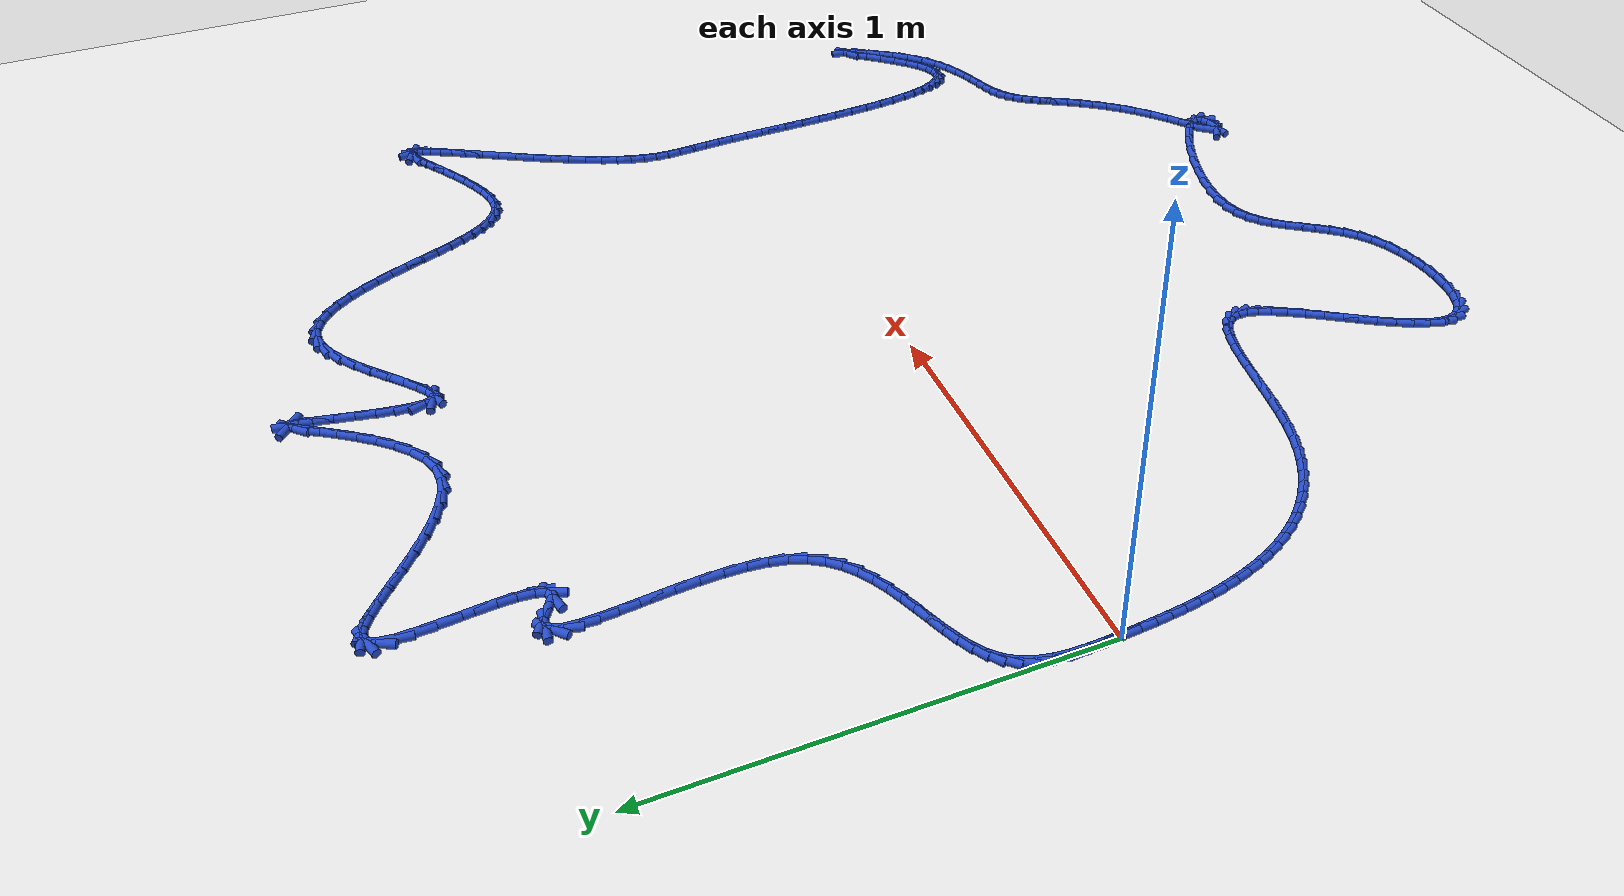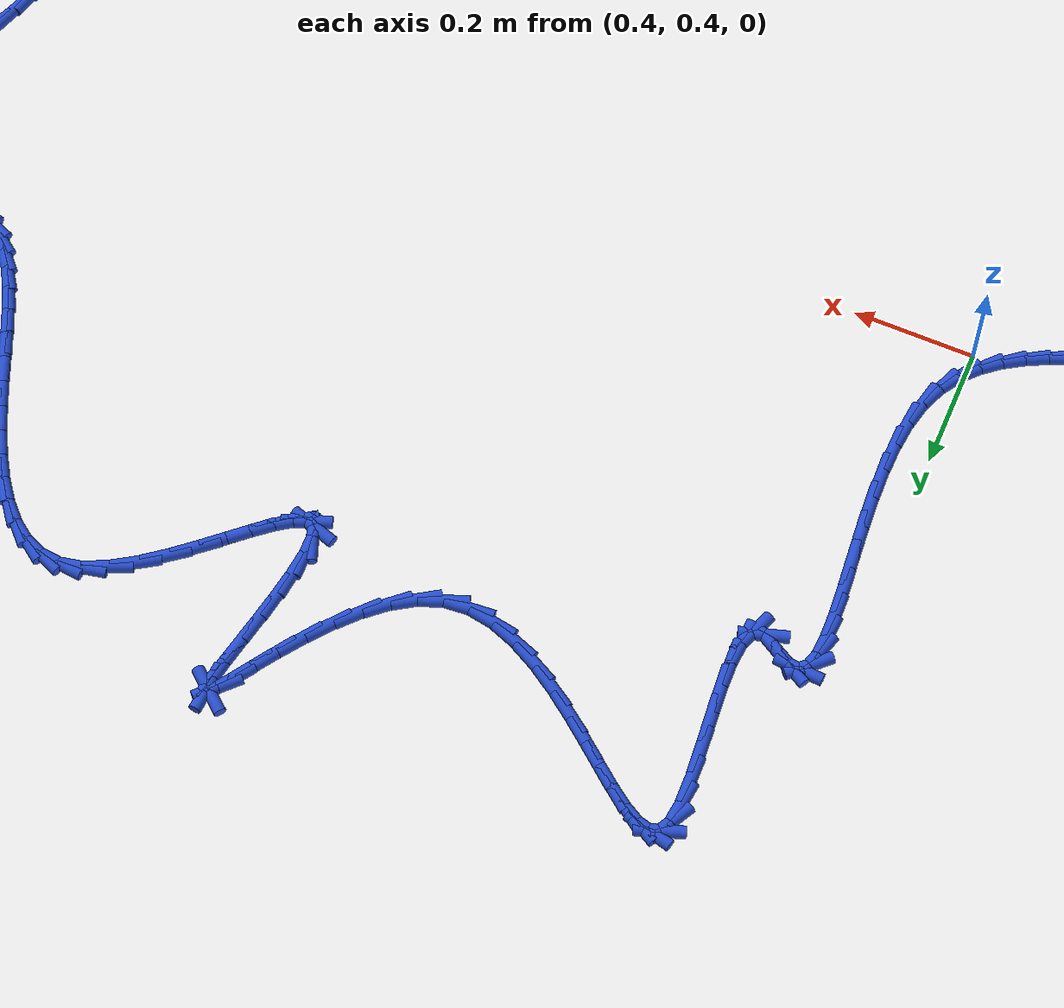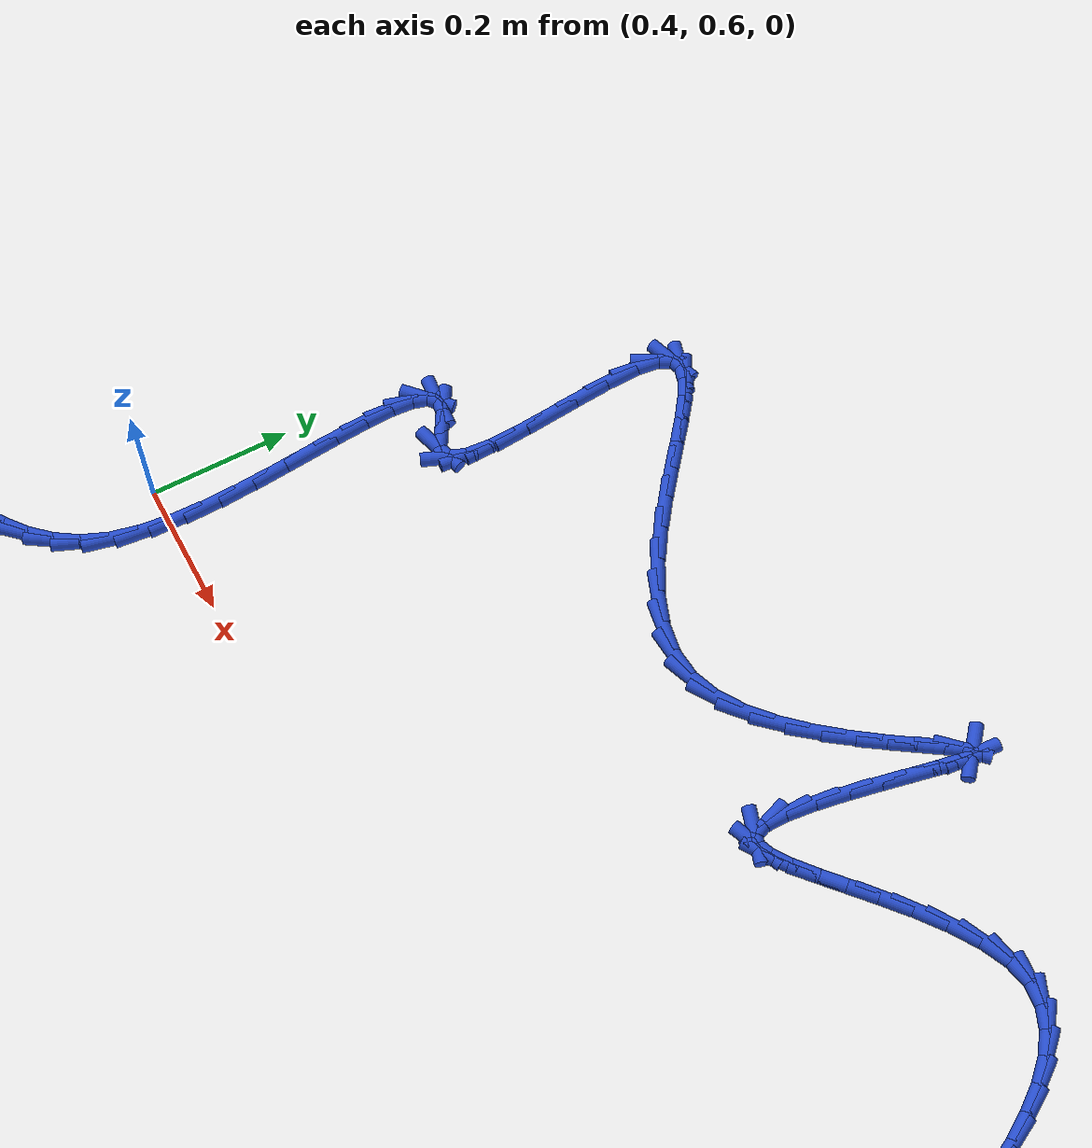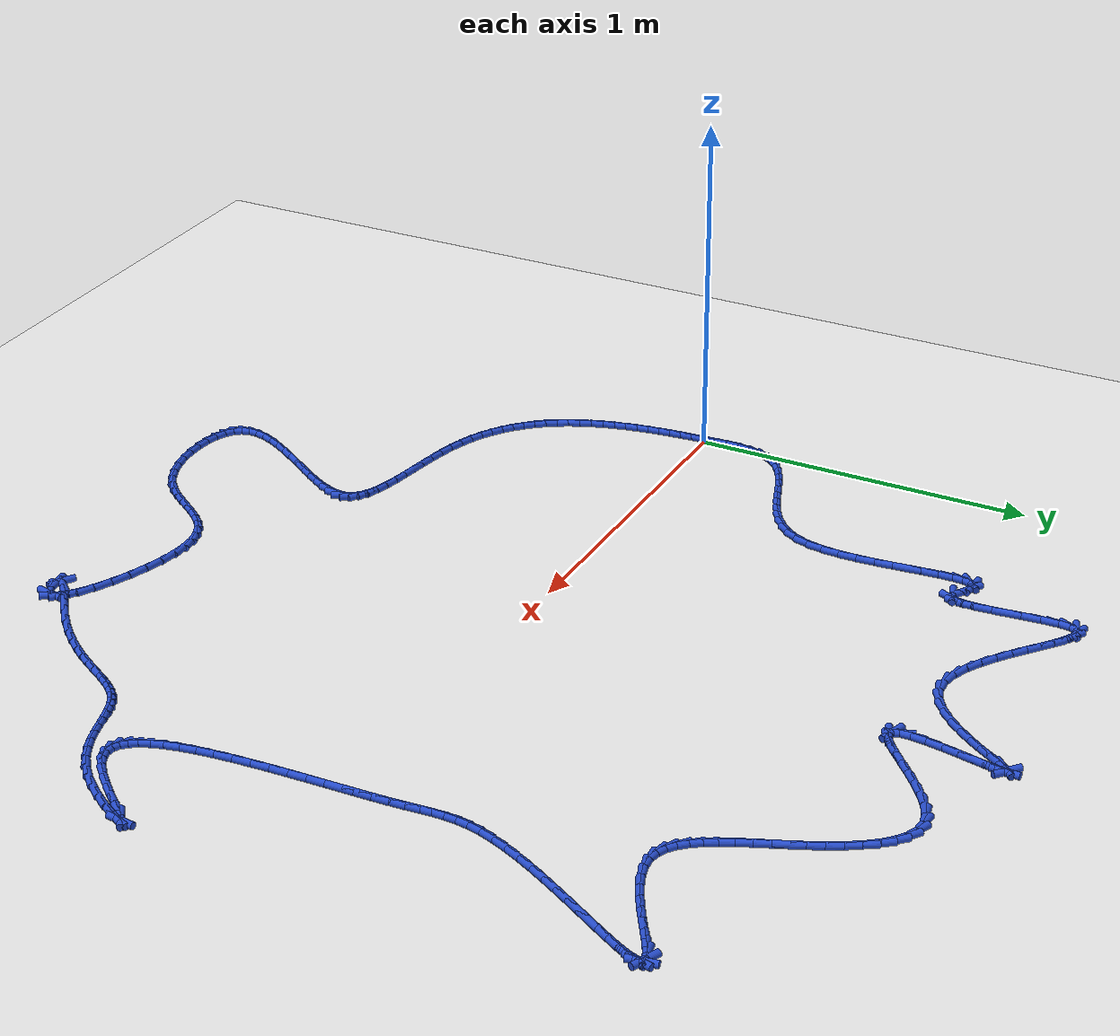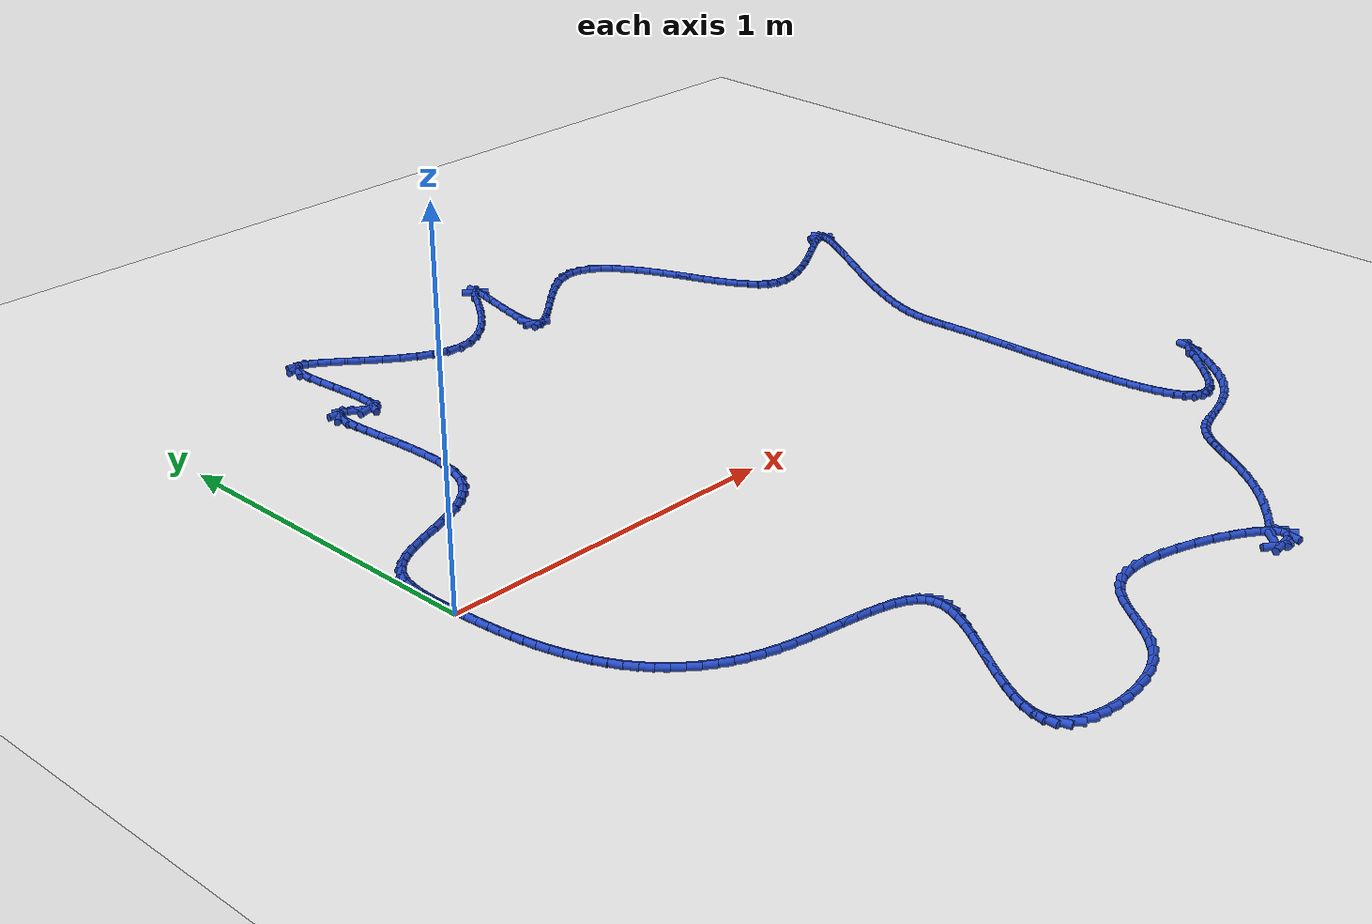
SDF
<sdf version="1.6">
 <world name="default">
  <light name="sun" type="directional">
   <pose>0 0 10 0 -0 0</pose>
   <diffuse>0.8 0.8 0.8 1</diffuse>
   <specular>0.2 0.2 0.2 1</specular>
   <attenuation>
    <range>1000</range>
    <constant>0.9</constant>
    <linear>0.01</linear>
    <quadratic>0.001</quadratic>
   </attenuation>
   <direction>-0.5 0.1 -0.9</direction>
  </light>
  <model name="ground_plane">
   <static>1</static>
   <link name="link">
    <collision name="collision">
     <geometry><plane><normal>0 0 1</normal><size>100 100</size></plane></geometry>
     <surface><friction><ode><mu>100</mu><mu2>50</mu2></ode></friction></surface>
    </collision>
    <visual name="visual">
     <cast_shadows>0</cast_shadows>
     <geometry><plane><normal>0 0 1</normal><size>100 100</size></plane></geometry>
     <material>
      <script><uri>file://media/materials/scripts/gazebo.material</uri><name>Gazebo/WhiteGlow</name></script>
     </material>
    </visual>
   </link>
  </model>
  <gravity>0 0 -9.8</gravity>
  <magnetic_field>6e-06 2.3e-05 -4.2e-05</magnetic_field>
  <atmosphere type="adiabatic"/>
  <physics name="default_physics" default="0" type="ode">
   <max_step_size>0.001</max_step_size>
   <real_time_factor>1</real_time_factor>
   <real_time_update_rate>1000</real_time_update_rate>
  </physics>
  <scene><ambient>0.4 0.4 0.4 1</ambient><background>0.7 0.7 0.7 1</background><shadows>1</shadows></scene>
  <spherical_coordinates>
   <surface_model>EARTH_WGS84</surface_model>
   <latitude_deg>0</latitude_deg>
   <longitude_deg>0</longitude_deg>
   <elevation>0</elevation>
   <heading_deg>0</heading_deg>
  </spherical_coordinates>
  <model name="line">
   <link name="link_0">
    <pose>4.5536491244391186e-17 -6.938893903907228e-18 0.01 0 1.57 -1.516350426905177</pose>
    <collision name="collision">
     <geometry><cylinder><radius>0.01</radius><length>0.08</length></cylinder></geometry>
    </collision>
    <visual name="visual">
     <material>
      <script><name>Gazebo/Blue</name><uri>file://media/materials/scripts/gazebo.material</uri></script>
     </material>
     <geometry><cylinder><radius>0.01</radius><length>0.08</length></cylinder></geometry>
    </visual>
   </link>
   <link name="link_1">
    <pose>-0.0020344990138612793 0.03733041962966487 0.01 0 1.57 -1.5432978315503292</pose>
    <collision name="collision">
     <geometry><cylinder><radius>0.01</radius><length>0.08</length></cylinder></geometry>
    </collision>
    <visual name="visual">
     <material>
      <script><name>Gazebo/Blue</name><uri>file://media/materials/scripts/gazebo.material</uri></script>
     </material>
     <geometry><cylinder><radius>0.01</radius><length>0.08</length></cylinder></geometry>
    </visual>
   </link>
   <link name="link_2">
    <pose>-0.003068716779485569 0.07493091604792003 0.01 0 1.57 1.547667495248963</pose>
    <collision name="collision">
     <geometry><cylinder><radius>0.01</radius><length>0.08</length></cylinder></geometry>
    </collision>
    <visual name="visual">
     <material>
      <script><name>Gazebo/Blue</name><uri>file://media/materials/scripts/gazebo.material</uri></script>
     </material>
     <geometry><cylinder><radius>0.01</radius><length>0.08</length></cylinder></geometry>
    </visual>
   </link>
   <link name="link_3">
    <pose>-0.0022136687239871274 0.1118932494490726 0.01 0 1.57 1.4685645919546335</pose>
    <collision name="collision">
     <geometry><cylinder><radius>0.01</radius><length>0.08</length></cylinder></geometry>
    </collision>
    <visual name="visual">
     <material>
      <script><name>Gazebo/Blue</name><uri>file://media/materials/scripts/gazebo.material</uri></script>
     </material>
     <geometry><cylinder><radius>0.01</radius><length>0.08</length></cylinder></geometry>
    </visual>
   </link>
   <link name="link_4">
    <pose>0.0014196297255197436 0.14730918002742974 0.01 0 1.57 1.3528270540345078</pose>
    <collision name="collision">
     <geometry><cylinder><radius>0.01</radius><length>0.08</length></cylinder></geometry>
    </collision>
    <visual name="visual">
     <material>
      <script><name>Gazebo/Blue</name><uri>file://media/materials/scripts/gazebo.material</uri></script>
     </material>
     <geometry><cylinder><radius>0.01</radius><length>0.08</length></cylinder></geometry>
    </visual>
   </link>
   <link name="link_5">
    <pose>0.008720163141920746 0.1802704679772984 0.01 0 1.57 1.1897835376856196</pose>
    <collision name="collision">
     <geometry><cylinder><radius>0.01</radius><length>0.08</length></cylinder></geometry>
    </collision>
    <visual name="visual">
     <material>
      <script><name>Gazebo/Blue</name><uri>file://media/materials/scripts/gazebo.material</uri></script>
     </material>
     <geometry><cylinder><radius>0.01</radius><length>0.08</length></cylinder></geometry>
    </visual>
   </link>
   <link name="link_6">
    <pose>0.020576916098101576 0.2098688734929859 0.01 0 1.57 0.9781830634710151</pose>
    <collision name="collision">
     <geometry><cylinder><radius>0.01</radius><length>0.08</length></cylinder></geometry>
    </collision>
    <visual name="visual">
     <material>
      <script><name>Gazebo/Blue</name><uri>file://media/materials/scripts/gazebo.material</uri></script>
     </material>
     <geometry><cylinder><radius>0.01</radius><length>0.08</length></cylinder></geometry>
    </visual>
   </link>
   <link name="link_7">
    <pose>0.03772929596335416 0.23534218453826133 0.01 0 1.57 0.7739168149898306</pose>
    <collision name="collision">
     <geometry><cylinder><radius>0.01</radius><length>0.08</length></cylinder></geometry>
    </collision>
    <visual name="visual">
     <material>
      <script><name>Gazebo/Blue</name><uri>file://media/materials/scripts/gazebo.material</uri></script>
     </material>
     <geometry><cylinder><radius>0.01</radius><length>0.08</length></cylinder></geometry>
    </visual>
   </link>
   <link name="link_8">
    <pose>0.05985455826962366 0.25696513628483125 0.01 0 1.57 0.6126361274357889</pose>
    <collision name="collision">
     <geometry><cylinder><radius>0.01</radius><length>0.08</length></cylinder></geometry>
    </collision>
    <visual name="visual">
     <material>
      <script><name>Gazebo/Blue</name><uri>file://media/materials/scripts/gazebo.material</uri></script>
     </material>
     <geometry><cylinder><radius>0.01</radius><length>0.08</length></cylinder></geometry>
    </visual>
   </link>
   <link name="link_9">
    <pose>0.08617033610541139 0.2754611796083885 0.01 0 1.57 0.4962904917748917</pose>
    <collision name="collision">
     <geometry><cylinder><radius>0.01</radius><length>0.08</length></cylinder></geometry>
    </collision>
    <visual name="visual">
     <material>
      <script><name>Gazebo/Blue</name><uri>file://media/materials/scripts/gazebo.material</uri></script>
     </material>
     <geometry><cylinder><radius>0.01</radius><length>0.08</length></cylinder></geometry>
    </visual>
   </link>
   <link name="link_10">
    <pose>0.1158924243633311 0.2915555599605287 0.01 0 1.57 0.41932789781211516</pose>
    <collision name="collision">
     <geometry><cylinder><radius>0.01</radius><length>0.08</length></cylinder></geometry>
    </collision>
    <visual name="visual">
     <material>
      <script><name>Gazebo/Blue</name><uri>file://media/materials/scripts/gazebo.material</uri></script>
     </material>
     <geometry><cylinder><radius>0.01</radius><length>0.08</length></cylinder></geometry>
    </visual>
   </link>
   <link name="link_11">
    <pose>0.1482366179359966 0.3059735227928481 0.01 0 1.57 0.37529912207708577</pose>
    <collision name="collision">
     <geometry><cylinder><radius>0.01</radius><length>0.08</length></cylinder></geometry>
    </collision>
    <visual name="visual">
     <material>
      <script><name>Gazebo/Blue</name><uri>file://media/materials/scripts/gazebo.material</uri></script>
     </material>
     <geometry><cylinder><radius>0.01</radius><length>0.08</length></cylinder></geometry>
    </visual>
   </link>
   <link name="link_12">
    <pose>0.18241871171602173 0.31944031355694236 0.01 0 1.57 0.3594533208540768</pose>
    <collision name="collision">
     <geometry><cylinder><radius>0.01</radius><length>0.08</length></cylinder></geometry>
    </collision>
    <visual name="visual">
     <material>
      <script><name>Gazebo/Blue</name><uri>file://media/materials/scripts/gazebo.material</uri></script>
     </material>
     <geometry><cylinder><radius>0.01</radius><length>0.08</length></cylinder></geometry>
    </visual>
   </link>
   <link name="link_13">
    <pose>0.21765450059602023 0.3326811777044076 0.01 0 1.57 0.3692406748582325</pose>
    <collision name="collision">
     <geometry><cylinder><radius>0.01</radius><length>0.08</length></cylinder></geometry>
    </collision>
    <visual name="visual">
     <material>
      <script><name>Gazebo/Blue</name><uri>file://media/materials/scripts/gazebo.material</uri></script>
     </material>
     <geometry><cylinder><radius>0.01</radius><length>0.08</length></cylinder></geometry>
    </visual>
   </link>
   <link name="link_14">
    <pose>0.25315977946860596 0.3464213606868398 0.01 0 1.57 0.4041380281691263</pose>
    <collision name="collision">
     <geometry><cylinder><radius>0.01</radius><length>0.08</length></cylinder></geometry>
    </collision>
    <visual name="visual">
     <material>
      <script><name>Gazebo/Blue</name><uri>file://media/materials/scripts/gazebo.material</uri></script>
     </material>
     <geometry><cylinder><radius>0.01</radius><length>0.08</length></cylinder></geometry>
    </visual>
   </link>
   <link name="link_15">
    <pose>0.2881503432263929 0.3613861079558349 0.01 0 1.57 0.4652783785459308</pose>
    <collision name="collision">
     <geometry><cylinder><radius>0.01</radius><length>0.08</length></cylinder></geometry>
    </collision>
    <visual name="visual">
     <material>
      <script><name>Gazebo/Blue</name><uri>file://media/materials/scripts/gazebo.material</uri></script>
     </material>
     <geometry><cylinder><radius>0.01</radius><length>0.08</length></cylinder></geometry>
    </visual>
   </link>
   <link name="link_16">
    <pose>0.32184198676199444 0.37830066496298875 0.01 0 1.57 0.5548204501725951</pose>
    <collision name="collision">
     <geometry><cylinder><radius>0.01</radius><length>0.08</length></cylinder></geometry>
    </collision>
    <visual name="visual">
     <material>
      <script><name>Gazebo/Blue</name><uri>file://media/materials/scripts/gazebo.material</uri></script>
     </material>
     <geometry><cylinder><radius>0.01</radius><length>0.08</length></cylinder></geometry>
    </visual>
   </link>
   <link name="link_17">
    <pose>0.35345050496802455 0.3978902771598971 0.01 0 1.57 0.6746764997015885</pose>
    <collision name="collision">
     <geometry><cylinder><radius>0.01</radius><length>0.08</length></cylinder></geometry>
    </collision>
    <visual name="visual">
     <material>
      <script><name>Gazebo/Blue</name><uri>file://media/materials/scripts/gazebo.material</uri></script>
     </material>
     <geometry><cylinder><radius>0.01</radius><length>0.08</length></cylinder></geometry>
    </visual>
   </link>
   <link name="link_18">
    <pose>0.3821916927370974 0.4208801899981567 0.01 0 1.57 0.8241834614877726</pose>
    <collision name="collision">
     <geometry><cylinder><radius>0.01</radius><length>0.08</length></cylinder></geometry>
    </collision>
    <visual name="visual">
     <material>
      <script><name>Gazebo/Blue</name><uri>file://media/materials/scripts/gazebo.material</uri></script>
     </material>
     <geometry><cylinder><radius>0.01</radius><length>0.08</length></cylinder></geometry>
    </visual>
   </link>
   <link name="link_19">
    <pose>0.4072813449618263 0.4479956489293626 0.01 0 1.57 0.9971562326662705</pose>
    <collision name="collision">
     <geometry><cylinder><radius>0.01</radius><length>0.08</length></cylinder></geometry>
    </collision>
    <visual name="visual">
     <material>
      <script><name>Gazebo/Blue</name><uri>file://media/materials/scripts/gazebo.material</uri></script>
     </material>
     <geometry><cylinder><radius>0.01</radius><length>0.08</length></cylinder></geometry>
    </visual>
   </link>
   <link name="link_20">
    <pose>0.42793525653482534 0.4799618994051113 0.01 0 1.57 1.1807488606486525</pose>
    <collision name="collision">
     <geometry><cylinder><radius>0.01</radius><length>0.08</length></cylinder></geometry>
    </collision>
    <visual name="visual">
     <material>
      <script><name>Gazebo/Blue</name><uri>file://media/materials/scripts/gazebo.material</uri></script>
     </material>
     <geometry><cylinder><radius>0.01</radius><length>0.08</length></cylinder></geometry>
    </visual>
   </link>
   <link name="link_21">
    <pose>0.44336926136309135 0.5175041380165123 0.01 0 1.57 1.3492541508872864</pose>
    <collision name="collision">
     <geometry><cylinder><radius>0.01</radius><length>0.08</length></cylinder></geometry>
    </collision>
    <visual name="visual">
     <material>
      <script><name>Gazebo/Blue</name><uri>file://media/materials/scripts/gazebo.material</uri></script>
     </material>
     <geometry><cylinder><radius>0.01</radius><length>0.08</length></cylinder></geometry>
    </visual>
   </link>
   <link name="link_22">
    <pose>0.4531465412502351 0.5609125528867348 0.01 0 1.57 1.469672239100606</pose>
    <collision name="collision">
     <geometry><cylinder><radius>0.01</radius><length>0.08</length></cylinder></geometry>
    </collision>
    <visual name="visual">
     <material>
      <script><name>Gazebo/Blue</name><uri>file://media/materials/scripts/gazebo.material</uri></script>
     </material>
     <geometry><cylinder><radius>0.01</radius><length>0.08</length></cylinder></geometry>
    </visual>
   </link>
   <link name="link_23">
    <pose>0.4580241715196973 0.6089821343962547 0.01 0 1.57 1.5514378879321196</pose>
    <collision name="collision">
     <geometry><cylinder><radius>0.01</radius><length>0.08</length></cylinder></geometry>
    </collision>
    <visual name="visual">
     <material>
      <script><name>Gazebo/Blue</name><uri>file://media/materials/scripts/gazebo.material</uri></script>
     </material>
     <geometry><cylinder><radius>0.01</radius><length>0.08</length></cylinder></geometry>
    </visual>
   </link>
   <link name="link_24">
    <pose>0.4590155392117438 0.6601868755383794 0.01 0 1.57 -1.5351861428149904</pose>
    <collision name="collision">
     <geometry><cylinder><radius>0.01</radius><length>0.08</length></cylinder></geometry>
    </collision>
    <visual name="visual">
     <material>
      <script><name>Gazebo/Blue</name><uri>file://media/materials/scripts/gazebo.material</uri></script>
     </material>
     <geometry><cylinder><radius>0.01</radius><length>0.08</length></cylinder></geometry>
    </visual>
   </link>
   <link name="link_25">
    <pose>0.4571340313666405 0.7130007693064166 0.01 0 1.57 -1.5001916576983663</pose>
    <collision name="collision">
     <geometry><cylinder><radius>0.01</radius><length>0.08</length></cylinder></geometry>
    </collision>
    <visual name="visual">
     <material>
      <script><name>Gazebo/Blue</name><uri>file://media/materials/scripts/gazebo.material</uri></script>
     </material>
     <geometry><cylinder><radius>0.01</radius><length>0.08</length></cylinder></geometry>
    </visual>
   </link>
   <link name="link_26">
    <pose>0.4533930350246533 0.7658978086936737 0.01 0 1.57 -1.4818821998179645</pose>
    <collision name="collision">
     <geometry><cylinder><radius>0.01</radius><length>0.08</length></cylinder></geometry>
    </collision>
    <visual name="visual">
     <material>
      <script><name>Gazebo/Blue</name><uri>file://media/materials/scripts/gazebo.material</uri></script>
     </material>
     <geometry><cylinder><radius>0.01</radius><length>0.08</length></cylinder></geometry>
    </visual>
   </link>
   <link name="link_27">
    <pose>0.4488059372260478 0.8173519866934584 0.01 0 1.57 -1.4798898143417276</pose>
    <collision name="collision">
     <geometry><cylinder><radius>0.01</radius><length>0.08</length></cylinder></geometry>
    </collision>
    <visual name="visual">
     <material>
      <script><name>Gazebo/Blue</name><uri>file://media/materials/scripts/gazebo.material</uri></script>
     </material>
     <geometry><cylinder><radius>0.01</radius><length>0.08</length></cylinder></geometry>
    </visual>
   </link>
   <link name="link_28">
    <pose>0.44438612501109 0.8658372962990784 0.01 0 1.57 -1.4972961525092776</pose>
    <collision name="collision">
     <geometry><cylinder><radius>0.01</radius><length>0.08</length></cylinder></geometry>
    </collision>
    <visual name="visual">
     <material>
      <script><name>Gazebo/Blue</name><uri>file://media/materials/scripts/gazebo.material</uri></script>
     </material>
     <geometry><cylinder><radius>0.01</radius><length>0.08</length></cylinder></geometry>
    </visual>
   </link>
   <link name="link_29">
    <pose>0.4411469854200457 0.9098277305038412 0.01 0 1.57 -1.543279116635272</pose>
    <collision name="collision">
     <geometry><cylinder><radius>0.01</radius><length>0.08</length></cylinder></geometry>
    </collision>
    <visual name="visual">
     <material>
      <script><name>Gazebo/Blue</name><uri>file://media/materials/scripts/gazebo.material</uri></script>
     </material>
     <geometry><cylinder><radius>0.01</radius><length>0.08</length></cylinder></geometry>
    </visual>
   </link>
   <link name="link_30">
    <pose>0.44010190549318073 0.9477972823010544 0.01 0 1.57 1.4998381603100779</pose>
    <collision name="collision">
     <geometry><cylinder><radius>0.01</radius><length>0.08</length></cylinder></geometry>
    </collision>
    <visual name="visual">
     <material>
      <script><name>Gazebo/Blue</name><uri>file://media/materials/scripts/gazebo.material</uri></script>
     </material>
     <geometry><cylinder><radius>0.01</radius><length>0.08</length></cylinder></geometry>
    </visual>
   </link>
   <link name="link_31">
    <pose>0.4422642722707609 0.9782199446840255 0.01 0 1.57 1.2802735325666097</pose>
    <collision name="collision">
     <geometry><cylinder><radius>0.01</radius><length>0.08</length></cylinder></geometry>
    </collision>
    <visual name="visual">
     <material>
      <script><name>Gazebo/Blue</name><uri>file://media/materials/scripts/gazebo.material</uri></script>
     </material>
     <geometry><cylinder><radius>0.01</radius><length>0.08</length></cylinder></geometry>
    </visual>
   </link>
   <link name="link_32">
    <pose>0.44864747279305206 0.9995697106460621 0.01 0 1.57 0.7466770147120076</pose>
    <collision name="collision">
     <geometry><cylinder><radius>0.01</radius><length>0.08</length></cylinder></geometry>
    </collision>
    <visual name="visual">
     <material>
      <script><name>Gazebo/Blue</name><uri>file://media/materials/scripts/gazebo.material</uri></script>
     </material>
     <geometry><cylinder><radius>0.01</radius><length>0.08</length></cylinder></geometry>
    </visual>
   </link>
   <link name="link_33">
    <pose>0.4602648941003201 1.010320573180472 0.01 0 1.57 -0.07676159061233405</pose>
    <collision name="collision">
     <geometry><cylinder><radius>0.01</radius><length>0.08</length></cylinder></geometry>
    </collision>
    <visual name="visual">
     <material>
      <script><name>Gazebo/Blue</name><uri>file://media/materials/scripts/gazebo.material</uri></script>
     </material>
     <geometry><cylinder><radius>0.01</radius><length>0.08</length></cylinder></geometry>
    </visual>
   </link>
   <link name="link_34">
    <pose>0.47812992323283066 1.0089465252805625 0.01 0 1.57 -0.5379317936606891</pose>
    <collision name="collision">
     <geometry><cylinder><radius>0.01</radius><length>0.08</length></cylinder></geometry>
    </collision>
    <visual name="visual">
     <material>
      <script><name>Gazebo/Blue</name><uri>file://media/materials/scripts/gazebo.material</uri></script>
     </material>
     <geometry><cylinder><radius>0.01</radius><length>0.08</length></cylinder></geometry>
    </visual>
   </link>
   <link name="link_35">
    <pose>0.5032322706969538 0.993969918694655 0.01 0 1.57 -0.5311312374379878</pose>
    <collision name="collision">
     <geometry><cylinder><radius>0.01</radius><length>0.08</length></cylinder></geometry>
    </collision>
    <visual name="visual">
     <material>
      <script><name>Gazebo/Blue</name><uri>file://media/materials/scripts/gazebo.material</uri></script>
     </material>
     <geometry><cylinder><radius>0.01</radius><length>0.08</length></cylinder></geometry>
    </visual>
   </link>
   <link name="link_36">
    <pose>0.5293442271808474 0.9786307733605706 0.01 0 1.57 0.2976537084486274</pose>
    <collision name="collision">
     <geometry><cylinder><radius>0.01</radius><length>0.08</length></cylinder></geometry>
    </collision>
    <visual name="visual">
     <material>
      <script><name>Gazebo/Blue</name><uri>file://media/materials/scripts/gazebo.material</uri></script>
     </material>
     <geometry><cylinder><radius>0.01</radius><length>0.08</length></cylinder></geometry>
    </visual>
   </link>
   <link name="link_37">
    <pose>0.5462599910329452 0.9838199766287489 0.01 0 1.57 1.195057549474425</pose>
    <collision name="collision">
     <geometry><cylinder><radius>0.01</radius><length>0.08</length></cylinder></geometry>
    </collision>
    <visual name="visual">
     <material>
      <script><name>Gazebo/Blue</name><uri>file://media/materials/scripts/gazebo.material</uri></script>
     </material>
     <geometry><cylinder><radius>0.01</radius><length>0.08</length></cylinder></geometry>
    </visual>
   </link>
   <link name="link_38">
    <pose>0.5552372002120606 1.0065770431607142 0.01 0 1.57 1.4927213225593474</pose>
    <collision name="collision">
     <geometry><cylinder><radius>0.01</radius><length>0.08</length></cylinder></geometry>
    </collision>
    <visual name="visual">
     <material>
      <script><name>Gazebo/Blue</name><uri>file://media/materials/scripts/gazebo.material</uri></script>
     </material>
     <geometry><cylinder><radius>0.01</radius><length>0.08</length></cylinder></geometry>
    </visual>
   </link>
   <link name="link_39">
    <pose>0.5580728977265976 1.042823385247488 0.01 0 1.57 -1.537762590267961</pose>
    <collision name="collision">
     <geometry><cylinder><radius>0.01</radius><length>0.08</length></cylinder></geometry>
    </collision>
    <visual name="visual">
     <material>
      <script><name>Gazebo/Blue</name><uri>file://media/materials/scripts/gazebo.material</uri></script>
     </material>
     <geometry><cylinder><radius>0.01</radius><length>0.08</length></cylinder></geometry>
    </visual>
   </link>
   <link name="link_40">
    <pose>0.5565641265849606 1.0884804151800913 0.01 0 1.57 -1.4914132713912989</pose>
    <collision name="collision">
     <geometry><cylinder><radius>0.01</radius><length>0.08</length></cylinder></geometry>
    </collision>
    <visual name="visual">
     <material>
      <script><name>Gazebo/Blue</name><uri>file://media/materials/scripts/gazebo.material</uri></script>
     </material>
     <geometry><cylinder><radius>0.01</radius><length>0.08</length></cylinder></geometry>
    </visual>
   </link>
   <link name="link_41">
    <pose>0.5525079297955532 1.1394695452495438 0.01 0 1.57 -1.47904971407833</pose>
    <collision name="collision">
     <geometry><cylinder><radius>0.01</radius><length>0.08</length></cylinder></geometry>
    </collision>
    <visual name="visual">
     <material>
      <script><name>Gazebo/Blue</name><uri>file://media/materials/scripts/gazebo.material</uri></script>
     </material>
     <geometry><cylinder><radius>0.01</radius><length>0.08</length></cylinder></geometry>
    </visual>
   </link>
   <link name="link_42">
    <pose>0.54770135036678 1.1917121877468675 0.01 0 1.57 -1.4948579686003254</pose>
    <collision name="collision">
     <geometry><cylinder><radius>0.01</radius><length>0.08</length></cylinder></geometry>
    </collision>
    <visual name="visual">
     <material>
      <script><name>Gazebo/Blue</name><uri>file://media/materials/scripts/gazebo.material</uri></script>
     </material>
     <geometry><cylinder><radius>0.01</radius><length>0.08</length></cylinder></geometry>
    </visual>
   </link>
   <link name="link_43">
    <pose>0.543941431307045 1.2411297549630824 0.01 0 1.57 -1.5492486967942585</pose>
    <collision name="collision">
     <geometry><cylinder><radius>0.01</radius><length>0.08</length></cylinder></geometry>
    </collision>
    <visual name="visual">
     <material>
      <script><name>Gazebo/Blue</name><uri>file://media/materials/scripts/gazebo.material</uri></script>
     </material>
     <geometry><cylinder><radius>0.01</radius><length>0.08</length></cylinder></geometry>
    </visual>
   </link>
   <link name="link_44">
    <pose>0.5430252156247518 1.2836436591892102 0.01 0 1.57 1.4532387338493584</pose>
    <collision name="collision">
     <geometry><cylinder><radius>0.01</radius><length>0.08</length></cylinder></geometry>
    </collision>
    <visual name="visual">
     <material>
      <script><name>Gazebo/Blue</name><uri>file://media/materials/scripts/gazebo.material</uri></script>
     </material>
     <geometry><cylinder><radius>0.01</radius><length>0.08</length></cylinder></geometry>
    </visual>
   </link>
   <link name="link_45">
    <pose>0.5467493048111051 1.315176441488841 0.01 0 1.57 1.0748273457671325</pose>
    <collision name="collision">
     <geometry><cylinder><radius>0.01</radius><length>0.08</length></cylinder></geometry>
    </collision>
    <visual name="visual">
     <material>
      <script><name>Gazebo/Blue</name><uri>file://media/materials/scripts/gazebo.material</uri></script>
     </material>
     <geometry><cylinder><radius>0.01</radius><length>0.08</length></cylinder></geometry>
    </visual>
   </link>
   <link name="link_46">
    <pose>0.5563870217666208 1.3329884447594325 0.01 0 1.57 0.3323990029920479</pose>
    <collision name="collision">
     <geometry><cylinder><radius>0.01</radius><length>0.08</length></cylinder></geometry>
    </collision>
    <visual name="visual">
     <material>
      <script><name>Gazebo/Blue</name><uri>file://media/materials/scripts/gazebo.material</uri></script>
     </material>
     <geometry><cylinder><radius>0.01</radius><length>0.08</length></cylinder></geometry>
    </visual>
   </link>
   <link name="link_47">
    <pose>0.571675932542274 1.338266292021979 0.01 0 1.57 -0.2566521204653958</pose>
    <collision name="collision">
     <geometry><cylinder><radius>0.01</radius><length>0.08</length></cylinder></geometry>
    </collision>
    <visual name="visual">
     <material>
      <script><name>Gazebo/Blue</name><uri>file://media/materials/scripts/gazebo.material</uri></script>
     </material>
     <geometry><cylinder><radius>0.01</radius><length>0.08</length></cylinder></geometry>
    </visual>
   </link>
   <link name="link_48">
    <pose>0.5920733062352094 1.3329132069487015 0.01 0 1.57 -0.5135768854988078</pose>
    <collision name="collision">
     <geometry><cylinder><radius>0.01</radius><length>0.08</length></cylinder></geometry>
    </collision>
    <visual name="visual">
     <material>
      <script><name>Gazebo/Blue</name><uri>file://media/materials/scripts/gazebo.material</uri></script>
     </material>
     <geometry><cylinder><radius>0.01</radius><length>0.08</length></cylinder></geometry>
    </visual>
   </link>
   <link name="link_49">
    <pose>0.617036411942572 1.3188324132118214 0.01 0 1.57 -0.6248242220848798</pose>
    <collision name="collision">
     <geometry><cylinder><radius>0.01</radius><length>0.08</length></cylinder></geometry>
    </collision>
    <visual name="visual">
     <material>
      <script><name>Gazebo/Blue</name><uri>file://media/materials/scripts/gazebo.material</uri></script>
     </material>
     <geometry><cylinder><radius>0.01</radius><length>0.08</length></cylinder></geometry>
    </visual>
   </link>
   <link name="link_50">
    <pose>0.6460225187615066 1.2979271344835617 0.01 0 1.57 -0.6719822785928745</pose>
    <collision name="collision">
     <geometry><cylinder><radius>0.01</radius><length>0.08</length></cylinder></geometry>
    </collision>
    <visual name="visual">
     <material>
      <script><name>Gazebo/Blue</name><uri>file://media/materials/scripts/gazebo.material</uri></script>
     </material>
     <geometry><cylinder><radius>0.01</radius><length>0.08</length></cylinder></geometry>
    </visual>
   </link>
   <link name="link_51">
    <pose>0.6784888957891578 1.2721005944361439 0.01 0 1.57 -0.6836574019877206</pose>
    <collision name="collision">
     <geometry><cylinder><radius>0.01</radius><length>0.08</length></cylinder></geometry>
    </collision>
    <visual name="visual">
     <material>
      <script><name>Gazebo/Blue</name><uri>file://media/materials/scripts/gazebo.material</uri></script>
     </material>
     <geometry><cylinder><radius>0.01</radius><length>0.08</length></cylinder></geometry>
    </visual>
   </link>
   <link name="link_52">
    <pose>0.7138928121226714 1.2432560167417888 0.01 0 1.57 -0.670214420626298</pose>
    <collision name="collision">
     <geometry><cylinder><radius>0.01</radius><length>0.08</length></cylinder></geometry>
    </collision>
    <visual name="visual">
     <material>
      <script><name>Gazebo/Blue</name><uri>file://media/materials/scripts/gazebo.material</uri></script>
     </material>
     <geometry><cylinder><radius>0.01</radius><length>0.08</length></cylinder></geometry>
    </visual>
   </link>
   <link name="link_53">
    <pose>0.7516915368591915 1.213296625072719 0.01 0 1.57 -0.6342842632402688</pose>
    <collision name="collision">
     <geometry><cylinder><radius>0.01</radius><length>0.08</length></cylinder></geometry>
    </collision>
    <visual name="visual">
     <material>
      <script><name>Gazebo/Blue</name><uri>file://media/materials/scripts/gazebo.material</uri></script>
     </material>
     <geometry><cylinder><radius>0.01</radius><length>0.08</length></cylinder></geometry>
    </visual>
   </link>
   <link name="link_54">
    <pose>0.791342339095863 1.1841256431011566 0.01 0 1.57 -0.5738869354243196</pose>
    <collision name="collision">
     <geometry><cylinder><radius>0.01</radius><length>0.08</length></cylinder></geometry>
    </collision>
    <visual name="visual">
     <material>
      <script><name>Gazebo/Blue</name><uri>file://media/materials/scripts/gazebo.material</uri></script>
     </material>
     <geometry><cylinder><radius>0.01</radius><length>0.08</length></cylinder></geometry>
    </visual>
   </link>
   <link name="link_55">
    <pose>0.8323024879298315 1.1576462944993227 0.01 0 1.57 -0.4830324689933849</pose>
    <collision name="collision">
     <geometry><cylinder><radius>0.01</radius><length>0.08</length></cylinder></geometry>
    </collision>
    <visual name="visual">
     <material>
      <script><name>Gazebo/Blue</name><uri>file://media/materials/scripts/gazebo.material</uri></script>
     </material>
     <geometry><cylinder><radius>0.01</radius><length>0.08</length></cylinder></geometry>
    </visual>
   </link>
   <link name="link_56">
    <pose>0.8740292524582416 1.1357618029394396 0.01 0 1.57 -0.3515394751154033</pose>
    <collision name="collision">
     <geometry><cylinder><radius>0.01</radius><length>0.08</length></cylinder></geometry>
    </collision>
    <visual name="visual">
     <material>
      <script><name>Gazebo/Blue</name><uri>file://media/materials/scripts/gazebo.material</uri></script>
     </material>
     <geometry><cylinder><radius>0.01</radius><length>0.08</length></cylinder></geometry>
    </visual>
   </link>
   <link name="link_57">
    <pose>0.9159799017782378 1.1203753920937287 0.01 0 1.57 -0.16623458699434665</pose>
    <collision name="collision">
     <geometry><cylinder><radius>0.01</radius><length>0.08</length></cylinder></geometry>
    </collision>
    <visual name="visual">
     <material>
      <script><name>Gazebo/Blue</name><uri>file://media/materials/scripts/gazebo.material</uri></script>
     </material>
     <geometry><cylinder><radius>0.01</radius><length>0.08</length></cylinder></geometry>
    </visual>
   </link>
   <link name="link_58">
    <pose>0.9576117049869655 1.113390285634412 0.01 0 1.57 0.08123805987009364</pose>
    <collision name="collision">
     <geometry><cylinder><radius>0.01</radius><length>0.08</length></cylinder></geometry>
    </collision>
    <visual name="visual">
     <material>
      <script><name>Gazebo/Blue</name><uri>file://media/materials/scripts/gazebo.material</uri></script>
     </material>
     <geometry><cylinder><radius>0.01</radius><length>0.08</length></cylinder></geometry>
    </visual>
   </link>
   <link name="link_59">
    <pose>0.998381931960715 1.1167096852503764 0.01 0 1.57 0.35755066332058805</pose>
    <collision name="collision">
     <geometry><cylinder><radius>0.01</radius><length>0.08</length></cylinder></geometry>
    </collision>
    <visual name="visual">
     <material>
      <script><name>Gazebo/Blue</name><uri>file://media/materials/scripts/gazebo.material</uri></script>
     </material>
     <geometry><cylinder><radius>0.01</radius><length>0.08</length></cylinder></geometry>
    </visual>
   </link>
   <link name="link_60">
    <pose>1.0377765231723843 1.131427861648435 0.01 0 1.57 0.5729358258525719</pose>
    <collision name="collision">
     <geometry><cylinder><radius>0.01</radius><length>0.08</length></cylinder></geometry>
    </collision>
    <visual name="visual">
     <material>
      <script><name>Gazebo/Blue</name><uri>file://media/materials/scripts/gazebo.material</uri></script>
     </material>
     <geometry><cylinder><radius>0.01</radius><length>0.08</length></cylinder></geometry>
    </visual>
   </link>
   <link name="link_61">
    <pose>1.075385928826018 1.1556903795627251 0.01 0 1.57 0.7231617154315875</pose>
    <collision name="collision">
     <geometry><cylinder><radius>0.01</radius><length>0.08</length></cylinder></geometry>
    </collision>
    <visual name="visual">
     <material>
      <script><name>Gazebo/Blue</name><uri>file://media/materials/scripts/gazebo.material</uri></script>
     </material>
     <geometry><cylinder><radius>0.01</radius><length>0.08</length></cylinder></geometry>
    </visual>
   </link>
   <link name="link_62">
    <pose>1.1108244053441816 1.18697111949308 0.01 0 1.57 0.8274831755246523</pose>
    <collision name="collision">
     <geometry><cylinder><radius>0.01</radius><length>0.08</length></cylinder></geometry>
    </collision>
    <visual name="visual">
     <material>
      <script><name>Gazebo/Blue</name><uri>file://media/materials/scripts/gazebo.material</uri></script>
     </material>
     <geometry><cylinder><radius>0.01</radius><length>0.08</length></cylinder></geometry>
    </visual>
   </link>
   <link name="link_63">
    <pose>1.143706209149443 1.2227439619393339 0.01 0 1.57 0.9001349775339298</pose>
    <collision name="collision">
     <geometry><cylinder><radius>0.01</radius><length>0.08</length></cylinder></geometry>
    </collision>
    <visual name="visual">
     <material>
      <script><name>Gazebo/Blue</name><uri>file://media/materials/scripts/gazebo.material</uri></script>
     </material>
     <geometry><cylinder><radius>0.01</radius><length>0.08</length></cylinder></geometry>
    </visual>
   </link>
   <link name="link_64">
    <pose>1.1736455966643682 1.2604827874013207 0.01 0 1.57 0.9495675840042191</pose>
    <collision name="collision">
     <geometry><cylinder><radius>0.01</radius><length>0.08</length></cylinder></geometry>
    </collision>
    <visual name="visual">
     <material>
      <script><name>Gazebo/Blue</name><uri>file://media/materials/scripts/gazebo.material</uri></script>
     </material>
     <geometry><cylinder><radius>0.01</radius><length>0.08</length></cylinder></geometry>
    </visual>
   </link>
   <link name="link_65">
    <pose>1.200256824311524 1.2976614763788736 0.01 0 1.57 0.9793690054236679</pose>
    <collision name="collision">
     <geometry><cylinder><radius>0.01</radius><length>0.08</length></cylinder></geometry>
    </collision>
    <visual name="visual">
     <material>
      <script><name>Gazebo/Blue</name><uri>file://media/materials/scripts/gazebo.material</uri></script>
     </material>
     <geometry><cylinder><radius>0.01</radius><length>0.08</length></cylinder></geometry>
    </visual>
   </link>
   <link name="link_66">
    <pose>1.223154148513477 1.3317539093718265 0.01 0 1.57 0.9874027941162314</pose>
    <collision name="collision">
     <geometry><cylinder><radius>0.01</radius><length>0.08</length></cylinder></geometry>
    </collision>
    <visual name="visual">
     <material>
      <script><name>Gazebo/Blue</name><uri>file://media/materials/scripts/gazebo.material</uri></script>
     </material>
     <geometry><cylinder><radius>0.01</radius><length>0.08</length></cylinder></geometry>
    </visual>
   </link>
   <link name="link_67">
    <pose>1.2419518256927937 1.3602339668800127 0.01 0 1.57 0.9576595495632187</pose>
    <collision name="collision">
     <geometry><cylinder><radius>0.01</radius><length>0.08</length></cylinder></geometry>
    </collision>
    <visual name="visual">
     <material>
      <script><name>Gazebo/Blue</name><uri>file://media/materials/scripts/gazebo.material</uri></script>
     </material>
     <geometry><cylinder><radius>0.01</radius><length>0.08</length></cylinder></geometry>
    </visual>
   </link>
   <link name="link_68">
    <pose>1.256264112272041 1.3805755294032667 0.01 0 1.57 0.7977311711641077</pose>
    <collision name="collision">
     <geometry><cylinder><radius>0.01</radius><length>0.08</length></cylinder></geometry>
    </collision>
    <visual name="visual">
     <material>
      <script><name>Gazebo/Blue</name><uri>file://media/materials/scripts/gazebo.material</uri></script>
     </material>
     <geometry><cylinder><radius>0.01</radius><length>0.08</length></cylinder></geometry>
    </visual>
   </link>
   <link name="link_69">
    <pose>1.2657052646737854 1.3902524774414222 0.01 0 1.57 -0.6985106043687016</pose>
    <collision name="collision">
     <geometry><cylinder><radius>0.01</radius><length>0.08</length></cylinder></geometry>
    </collision>
    <visual name="visual">
     <material>
      <script><name>Gazebo/Blue</name><uri>file://media/materials/scripts/gazebo.material</uri></script>
     </material>
     <geometry><cylinder><radius>0.01</radius><length>0.08</length></cylinder></geometry>
    </visual>
   </link>
   <link name="link_70">
    <pose>1.2698895539854897 1.38673873923058 0.01 0 1.57 1.5092083684171693</pose>
    <collision name="collision">
     <geometry><cylinder><radius>0.01</radius><length>0.08</length></cylinder></geometry>
    </collision>
    <visual name="visual">
     <material>
      <script><name>Gazebo/Blue</name><uri>file://media/materials/scripts/gazebo.material</uri></script>
     </material>
     <geometry><cylinder><radius>0.01</radius><length>0.08</length></cylinder></geometry>
    </visual>
   </link>
   <link name="link_71">
    <pose>1.2687721077704281 1.368617778022861 0.01 0 1.57 1.398758770093922</pose>
    <collision name="collision">
     <geometry><cylinder><radius>0.01</radius><length>0.08</length></cylinder></geometry>
    </collision>
    <visual name="visual">
     <material>
      <script><name>Gazebo/Blue</name><uri>file://media/materials/scripts/gazebo.material</uri></script>
     </material>
     <geometry><cylinder><radius>0.01</radius><length>0.08</length></cylinder></geometry>
    </visual>
   </link>
   <link name="link_72">
    <pose>1.263530957244736 1.3384537777559522 0.01 0 1.57 1.3693697978223787</pose>
    <collision name="collision">
     <geometry><cylinder><radius>0.01</radius><length>0.08</length></cylinder></geometry>
    </collision>
    <visual name="visual">
     <material>
      <script><name>Gazebo/Blue</name><uri>file://media/materials/scripts/gazebo.material</uri></script>
     </material>
     <geometry><cylinder><radius>0.01</radius><length>0.08</length></cylinder></geometry>
    </visual>
   </link>
   <link name="link_73">
    <pose>1.2556182831749525 1.2997033171066312 0.01 0 1.57 1.3656132691662246</pose>
    <collision name="collision">
     <geometry><cylinder><radius>0.01</radius><length>0.08</length></cylinder></geometry>
    </collision>
    <visual name="visual">
     <material>
      <script><name>Gazebo/Blue</name><uri>file://media/materials/scripts/gazebo.material</uri></script>
     </material>
     <geometry><cylinder><radius>0.01</radius><length>0.08</length></cylinder></geometry>
    </visual>
   </link>
   <link name="link_74">
    <pose>1.2464862663276168 1.2558229747516763 0.01 0 1.57 1.3778700940404252</pose>
    <collision name="collision">
     <geometry><cylinder><radius>0.01</radius><length>0.08</length></cylinder></geometry>
    </collision>
    <visual name="visual">
     <material>
      <script><name>Gazebo/Blue</name><uri>file://media/materials/scripts/gazebo.material</uri></script>
     </material>
     <geometry><cylinder><radius>0.01</radius><length>0.08</length></cylinder></geometry>
    </visual>
   </link>
   <link name="link_75">
    <pose>1.2375870874692683 1.2102693293678641 0.01 0 1.57 1.40744654913582</pose>
    <collision name="collision">
     <geometry><cylinder><radius>0.01</radius><length>0.08</length></cylinder></geometry>
    </collision>
    <visual name="visual">
     <material>
      <script><name>Gazebo/Blue</name><uri>file://media/materials/scripts/gazebo.material</uri></script>
     </material>
     <geometry><cylinder><radius>0.01</radius><length>0.08</length></cylinder></geometry>
    </visual>
   </link>
   <link name="link_76">
    <pose>1.2303729273664459 1.1664989596319737 0.01 0 1.57 1.4653773698275474</pose>
    <collision name="collision">
     <geometry><cylinder><radius>0.01</radius><length>0.08</length></cylinder></geometry>
    </collision>
    <visual name="visual">
     <material>
      <script><name>Gazebo/Blue</name><uri>file://media/materials/scripts/gazebo.material</uri></script>
     </material>
     <geometry><cylinder><radius>0.01</radius><length>0.08</length></cylinder></geometry>
    </visual>
   </link>
   <link name="link_77">
    <pose>1.2262959667856892 1.1279684442207814 0.01 0 1.57 -1.5536223671169886</pose>
    <collision name="collision">
     <geometry><cylinder><radius>0.01</radius><length>0.08</length></cylinder></geometry>
    </collision>
    <visual name="visual">
     <material>
      <script><name>Gazebo/Blue</name><uri>file://media/materials/scripts/gazebo.material</uri></script>
     </material>
     <geometry><cylinder><radius>0.01</radius><length>0.08</length></cylinder></geometry>
    </visual>
   </link>
   <link name="link_78">
    <pose>1.2268083864935366 1.098134361811065 0.01 0 1.57 -1.2167855442701356</pose>
    <collision name="collision">
     <geometry><cylinder><radius>0.01</radius><length>0.08</length></cylinder></geometry>
    </collision>
    <visual name="visual">
     <material>
      <script><name>Gazebo/Blue</name><uri>file://media/materials/scripts/gazebo.material</uri></script>
     </material>
     <geometry><cylinder><radius>0.01</radius><length>0.08</length></cylinder></geometry>
    </visual>
   </link>
   <link name="link_79">
    <pose>1.2333523058330418 1.080428012693828 0.01 0 1.57 -0.3039822398307355</pose>
    <collision name="collision">
     <geometry><cylinder><radius>0.01</radius><length>0.08</length></cylinder></geometry>
    </collision>
    <visual name="visual">
     <material>
      <script><name>Gazebo/Blue</name><uri>file://media/materials/scripts/gazebo.material</uri></script>
     </material>
     <geometry><cylinder><radius>0.01</radius><length>0.08</length></cylinder></geometry>
    </visual>
   </link>
   <link name="link_80">
    <pose>1.246573677518374 1.0762804029459523 0.01 0 1.57 0.36931523468999916</pose>
    <collision name="collision">
     <geometry><cylinder><radius>0.01</radius><length>0.08</length></cylinder></geometry>
    </collision>
    <visual name="visual">
     <material>
      <script><name>Gazebo/Blue</name><uri>file://media/materials/scripts/gazebo.material</uri></script>
     </material>
     <geometry><cylinder><radius>0.01</radius><length>0.08</length></cylinder></geometry>
    </visual>
   </link>
   <link name="link_81">
    <pose>1.2657587817118034 1.0837064884859733 0.01 0 1.57 0.6015300312243337</pose>
    <collision name="collision">
     <geometry><cylinder><radius>0.01</radius><length>0.08</length></cylinder></geometry>
    </collision>
    <visual name="visual">
     <material>
      <script><name>Gazebo/Blue</name><uri>file://media/materials/scripts/gazebo.material</uri></script>
     </material>
     <geometry><cylinder><radius>0.01</radius><length>0.08</length></cylinder></geometry>
    </visual>
   </link>
   <link name="link_82">
    <pose>1.2900609147155186 1.1003871157178564 0.01 0 1.57 0.6907101843505407</pose>
    <collision name="collision">
     <geometry><cylinder><radius>0.01</radius><length>0.08</length></cylinder></geometry>
    </collision>
    <visual name="visual">
     <material>
      <script><name>Gazebo/Blue</name><uri>file://media/materials/scripts/gazebo.material</uri></script>
     </material>
     <geometry><cylinder><radius>0.01</radius><length>0.08</length></cylinder></geometry>
    </visual>
   </link>
   <link name="link_83">
    <pose>1.3186333728317066 1.1240031310455665 0.01 0 1.57 0.7229866450906738</pose>
    <collision name="collision">
     <geometry><cylinder><radius>0.01</radius><length>0.08</length></cylinder></geometry>
    </collision>
    <visual name="visual">
     <material>
      <script><name>Gazebo/Blue</name><uri>file://media/materials/scripts/gazebo.material</uri></script>
     </material>
     <geometry><cylinder><radius>0.01</radius><length>0.08</length></cylinder></geometry>
    </visual>
   </link>
   <link name="link_84">
    <pose>1.3506294523625566 1.1522353808730694 0.01 0 1.57 0.723365382916249</pose>
    <collision name="collision">
     <geometry><cylinder><radius>0.01</radius><length>0.08</length></cylinder></geometry>
    </collision>
    <visual name="visual">
     <material>
      <script><name>Gazebo/Blue</name><uri>file://media/materials/scripts/gazebo.material</uri></script>
     </material>
     <geometry><cylinder><radius>0.01</radius><length>0.08</length></cylinder></geometry>
    </visual>
   </link>
   <link name="link_85">
    <pose>1.3852024496102557 1.18276471160433 0.01 0 1.57 0.6988626458921552</pose>
    <collision name="collision">
     <geometry><cylinder><radius>0.01</radius><length>0.08</length></cylinder></geometry>
    </collision>
    <visual name="visual">
     <material>
      <script><name>Gazebo/Blue</name><uri>file://media/materials/scripts/gazebo.material</uri></script>
     </material>
     <geometry><cylinder><radius>0.01</radius><length>0.08</length></cylinder></geometry>
    </visual>
   </link>
   <link name="link_86">
    <pose>1.4215056608769936 1.2132719696433147 0.01 0 1.57 0.6482341323624207</pose>
    <collision name="collision">
     <geometry><cylinder><radius>0.01</radius><length>0.08</length></cylinder></geometry>
    </collision>
    <visual name="visual">
     <material>
      <script><name>Gazebo/Blue</name><uri>file://media/materials/scripts/gazebo.material</uri></script>
     </material>
     <geometry><cylinder><radius>0.01</radius><length>0.08</length></cylinder></geometry>
    </visual>
   </link>
   <link name="link_87">
    <pose>1.4586923824649578 1.241438001393988 0.01 0 1.57 0.5632404988815849</pose>
    <collision name="collision">
     <geometry><cylinder><radius>0.01</radius><length>0.08</length></cylinder></geometry>
    </collision>
    <visual name="visual">
     <material>
      <script><name>Gazebo/Blue</name><uri>file://media/materials/scripts/gazebo.material</uri></script>
     </material>
     <geometry><cylinder><radius>0.01</radius><length>0.08</length></cylinder></geometry>
    </visual>
   </link>
   <link name="link_88">
    <pose>1.4959159106763367 1.2649436532603164 0.01 0 1.57 0.4260462333537006</pose>
    <collision name="collision">
     <geometry><cylinder><radius>0.01</radius><length>0.08</length></cylinder></geometry>
    </collision>
    <visual name="visual">
     <material>
      <script><name>Gazebo/Blue</name><uri>file://media/materials/scripts/gazebo.material</uri></script>
     </material>
     <geometry><cylinder><radius>0.01</radius><length>0.08</length></cylinder></geometry>
    </visual>
   </link>
   <link name="link_89">
    <pose>1.5323295418133176 1.2814697716462642 0.01 0 1.57 0.20534554346475045</pose>
    <collision name="collision">
     <geometry><cylinder><radius>0.01</radius><length>0.08</length></cylinder></geometry>
    </collision>
    <visual name="visual">
     <material>
      <script><name>Gazebo/Blue</name><uri>file://media/materials/scripts/gazebo.material</uri></script>
     </material>
     <geometry><cylinder><radius>0.01</radius><length>0.08</length></cylinder></geometry>
    </visual>
   </link>
   <link name="link_90">
    <pose>1.567089635826595 1.288709650074235 0.01 0 1.57 -0.09607439442499995</pose>
    <collision name="collision">
     <geometry><cylinder><radius>0.01</radius><length>0.08</length></cylinder></geometry>
    </collision>
    <visual name="visual">
     <material>
      <script><name>Gazebo/Blue</name><uri>file://media/materials/scripts/gazebo.material</uri></script>
     </material>
     <geometry><cylinder><radius>0.01</radius><length>0.08</length></cylinder></geometry>
    </visual>
   </link>
   <link name="link_91">
    <pose>1.5996516130219725 1.28557161690283 0.01 0 1.57 -0.3874172694732243</pose>
    <collision name="collision">
     <geometry><cylinder><radius>0.01</radius><length>0.08</length></cylinder></geometry>
    </collision>
    <visual name="visual">
     <material>
      <script><name>Gazebo/Blue</name><uri>file://media/materials/scripts/gazebo.material</uri></script>
     </material>
     <geometry><cylinder><radius>0.01</radius><length>0.08</length></cylinder></geometry>
    </visual>
   </link>
   <link name="link_92">
    <pose>1.630016689404305 1.273181481933656 0.01 0 1.57 -0.6230113221757752</pose>
    <collision name="collision">
     <geometry><cylinder><radius>0.01</radius><length>0.08</length></cylinder></geometry>
    </collision>
    <visual name="visual">
     <material>
      <script><name>Gazebo/Blue</name><uri>file://media/materials/scripts/gazebo.material</uri></script>
     </material>
     <geometry><cylinder><radius>0.01</radius><length>0.08</length></cylinder></geometry>
    </visual>
   </link>
   <link name="link_93">
    <pose>1.6582441629500086 1.2529010328155763 0.01 0 1.57 -0.7978565454737813</pose>
    <collision name="collision">
     <geometry><cylinder><radius>0.01</radius><length>0.08</length></cylinder></geometry>
    </collision>
    <visual name="visual">
     <material>
      <script><name>Gazebo/Blue</name><uri>file://media/materials/scripts/gazebo.material</uri></script>
     </material>
     <geometry><cylinder><radius>0.01</radius><length>0.08</length></cylinder></geometry>
    </visual>
   </link>
   <link name="link_94">
    <pose>1.6843933316354958 1.2260920571974543 0.01 0 1.57 -0.9243320538142196</pose>
    <collision name="collision">
     <geometry><cylinder><radius>0.01</radius><length>0.08</length></cylinder></geometry>
    </collision>
    <visual name="visual">
     <material>
      <script><name>Gazebo/Blue</name><uri>file://media/materials/scripts/gazebo.material</uri></script>
     </material>
     <geometry><cylinder><radius>0.01</radius><length>0.08</length></cylinder></geometry>
    </visual>
   </link>
   <link name="link_95">
    <pose>1.708523493437182 1.1941163427281538 0.01 0 1.57 -1.0160743895242792</pose>
    <collision name="collision">
     <geometry><cylinder><radius>0.01</radius><length>0.08</length></cylinder></geometry>
    </collision>
    <visual name="visual">
     <material>
      <script><name>Gazebo/Blue</name><uri>file://media/materials/scripts/gazebo.material</uri></script>
     </material>
     <geometry><cylinder><radius>0.01</radius><length>0.08</length></cylinder></geometry>
    </visual>
   </link>
   <link name="link_96">
    <pose>1.7306939463314799 1.1583356770565378 0.01 0 1.57 -1.0831982492757537</pose>
    <collision name="collision">
     <geometry><cylinder><radius>0.01</radius><length>0.08</length></cylinder></geometry>
    </collision>
    <visual name="visual">
     <material>
      <script><name>Gazebo/Blue</name><uri>file://media/materials/scripts/gazebo.material</uri></script>
     </material>
     <geometry><cylinder><radius>0.01</radius><length>0.08</length></cylinder></geometry>
    </visual>
   </link>
   <link name="link_97">
    <pose>1.7509659513090186 1.120108740271139 0.01 0 1.57 -1.1315955366389887</pose>
    <collision name="collision">
     <geometry><cylinder><radius>0.01</radius><length>0.08</length></cylinder></geometry>
    </collision>
    <visual name="visual">
     <material>
      <script><name>Gazebo/Blue</name><uri>file://media/materials/scripts/gazebo.material</uri></script>
     </material>
     <geometry><cylinder><radius>0.01</radius><length>0.08</length></cylinder></geometry>
    </visual>
   </link>
   <link name="link_98">
    <pose>1.7695386146684435 1.0805759956955598 0.01 0 1.57 -1.1631310975254268</pose>
    <collision name="collision">
     <geometry><cylinder><radius>0.01</radius><length>0.08</length></cylinder></geometry>
    </collision>
    <visual name="visual">
     <material>
      <script><name>Gazebo/Blue</name><uri>file://media/materials/scripts/gazebo.material</uri></script>
     </material>
     <geometry><cylinder><radius>0.01</radius><length>0.08</length></cylinder></geometry>
    </visual>
   </link>
   <link name="link_99">
    <pose>1.7868371159117076 1.0405200202387666 0.01 0 1.57 -1.1786880895584793</pose>
    <collision name="collision">
     <geometry><cylinder><radius>0.01</radius><length>0.08</length></cylinder></geometry>
    </collision>
    <visual name="visual">
     <material>
      <script><name>Gazebo/Blue</name><uri>file://media/materials/scripts/gazebo.material</uri></script>
     </material>
     <geometry><cylinder><radius>0.01</radius><length>0.08</length></cylinder></geometry>
    </visual>
   </link>
   <link name="link_100">
    <pose>1.8033076085232442 1.0006901878326295 0.01 0 1.57 -1.178214712655763</pose>
    <collision name="collision">
     <geometry><cylinder><radius>0.01</radius><length>0.08</length></cylinder></geometry>
    </collision>
    <visual name="visual">
     <material>
      <script><name>Gazebo/Blue</name><uri>file://media/materials/scripts/gazebo.material</uri></script>
     </material>
     <geometry><cylinder><radius>0.01</radius><length>0.08</length></cylinder></geometry>
    </visual>
   </link>
   <link name="link_101">
    <pose>1.8193962459874853 0.9618358724090186 0.01 0 1.57 -1.1604491172332083</pose>
    <collision name="collision">
     <geometry><cylinder><radius>0.01</radius><length>0.08</length></cylinder></geometry>
    </collision>
    <visual name="visual">
     <material>
      <script><name>Gazebo/Blue</name><uri>file://media/materials/scripts/gazebo.material</uri></script>
     </material>
     <geometry><cylinder><radius>0.01</radius><length>0.08</length></cylinder></geometry>
    </visual>
   </link>
   <link name="link_102">
    <pose>1.8355491817888654 0.9247064478998029 0.01 0 1.57 -1.122598542730923</pose>
    <collision name="collision">
     <geometry><cylinder><radius>0.01</radius><length>0.08</length></cylinder></geometry>
    </collision>
    <visual name="visual">
     <material>
      <script><name>Gazebo/Blue</name><uri>file://media/materials/scripts/gazebo.material</uri></script>
     </material>
     <geometry><cylinder><radius>0.01</radius><length>0.08</length></cylinder></geometry>
    </visual>
   </link>
   <link name="link_103">
    <pose>1.8522125694118179 0.8900512882368539 0.01 0 1.57 -1.0598638934474927</pose>
    <collision name="collision">
     <geometry><cylinder><radius>0.01</radius><length>0.08</length></cylinder></geometry>
    </collision>
    <visual name="visual">
     <material>
      <script><name>Gazebo/Blue</name><uri>file://media/materials/scripts/gazebo.material</uri></script>
     </material>
     <geometry><cylinder><radius>0.01</radius><length>0.08</length></cylinder></geometry>
    </visual>
   </link>
   <link name="link_104">
    <pose>1.8698325623407757 0.8586197673520409 0.01 0 1.57 -0.9649313113036356</pose>
    <collision name="collision">
     <geometry><cylinder><radius>0.01</radius><length>0.08</length></cylinder></geometry>
    </collision>
    <visual name="visual">
     <material>
      <script><name>Gazebo/Blue</name><uri>file://media/materials/scripts/gazebo.material</uri></script>
     </material>
     <geometry><cylinder><radius>0.01</radius><length>0.08</length></cylinder></geometry>
    </visual>
   </link>
   <link name="link_105">
    <pose>1.8888553140601725 0.8311612591772345 0.01 0 1.57 -0.8281272926689245</pose>
    <collision name="collision">
     <geometry><cylinder><radius>0.01</radius><length>0.08</length></cylinder></geometry>
    </collision>
    <visual name="visual">
     <material>
      <script><name>Gazebo/Blue</name><uri>file://media/materials/scripts/gazebo.material</uri></script>
     </material>
     <geometry><cylinder><radius>0.01</radius><length>0.08</length></cylinder></geometry>
    </visual>
   </link>
   <link name="link_106">
    <pose>1.9097269780544415 0.8084251376443047 0.01 0 1.57 -0.6404362878605853</pose>
    <collision name="collision">
     <geometry><cylinder><radius>0.01</radius><length>0.08</length></cylinder></geometry>
    </collision>
    <visual name="visual">
     <material>
      <script><name>Gazebo/Blue</name><uri>file://media/materials/scripts/gazebo.material</uri></script>
     </material>
     <geometry><cylinder><radius>0.01</radius><length>0.08</length></cylinder></geometry>
    </visual>
   </link>
   <link name="link_107">
    <pose>1.9328937078080162 0.7911607766851215 0.01 0 1.57 -0.40292772986061187</pose>
    <collision name="collision">
     <geometry><cylinder><radius>0.01</radius><length>0.08</length></cylinder></geometry>
    </collision>
    <visual name="visual">
     <material>
      <script><name>Gazebo/Blue</name><uri>file://media/materials/scripts/gazebo.material</uri></script>
     </material>
     <geometry><cylinder><radius>0.01</radius><length>0.08</length></cylinder></geometry>
    </visual>
   </link>
   <link name="link_108">
    <pose>1.958801656805329 0.7801175502315554 0.01 0 1.57 -0.13907480496183336</pose>
    <collision name="collision">
     <geometry><cylinder><radius>0.01</radius><length>0.08</length></cylinder></geometry>
    </collision>
    <visual name="visual">
     <material>
      <script><name>Gazebo/Blue</name><uri>file://media/materials/scripts/gazebo.material</uri></script>
     </material>
     <geometry><cylinder><radius>0.01</radius><length>0.08</length></cylinder></geometry>
    </visual>
   </link>
   <link name="link_109">
    <pose>1.9878969785308152 0.776044832215476 0.01 0 1.57 0.1023306690665531</pose>
    <collision name="collision">
     <geometry><cylinder><radius>0.01</radius><length>0.08</length></cylinder></geometry>
    </collision>
    <visual name="visual">
     <material>
      <script><name>Gazebo/Blue</name><uri>file://media/materials/scripts/gazebo.material</uri></script>
     </material>
     <geometry><cylinder><radius>0.01</radius><length>0.08</length></cylinder></geometry>
    </visual>
   </link>
   <link name="link_110">
    <pose>2.0204201757538427 0.7793846184911194 0.01 0 1.57 0.2700291150694442</pose>
    <collision name="collision">
     <geometry><cylinder><radius>0.01</radius><length>0.08</length></cylinder></geometry>
    </collision>
    <visual name="visual">
     <material>
      <script><name>Gazebo/Blue</name><uri>file://media/materials/scripts/gazebo.material</uri></script>
     </material>
     <geometry><cylinder><radius>0.01</radius><length>0.08</length></cylinder></geometry>
    </visual>
   </link>
   <link name="link_111">
    <pose>2.055645443124595 0.7891346019741866 0.01 0 1.57 0.37973209714804096</pose>
    <collision name="collision">
     <geometry><cylinder><radius>0.01</radius><length>0.08</length></cylinder></geometry>
    </collision>
    <visual name="visual">
     <material>
      <script><name>Gazebo/Blue</name><uri>file://media/materials/scripts/gazebo.material</uri></script>
     </material>
     <geometry><cylinder><radius>0.01</radius><length>0.08</length></cylinder></geometry>
    </visual>
   </link>
   <link name="link_112">
    <pose>2.092563409028925 0.8038686401797407 0.01 0 1.57 0.45276539629791684</pose>
    <collision name="collision">
     <geometry><cylinder><radius>0.01</radius><length>0.08</length></cylinder></geometry>
    </collision>
    <visual name="visual">
     <material>
      <script><name>Gazebo/Blue</name><uri>file://media/materials/scripts/gazebo.material</uri></script>
     </material>
     <geometry><cylinder><radius>0.01</radius><length>0.08</length></cylinder></geometry>
    </visual>
   </link>
   <link name="link_113">
    <pose>2.130164664535675 0.8221605348465617 0.01 0 1.57 0.5012399327119883</pose>
    <collision name="collision">
     <geometry><cylinder><radius>0.01</radius><length>0.08</length></cylinder></geometry>
    </collision>
    <visual name="visual">
     <material>
      <script><name>Gazebo/Blue</name><uri>file://media/materials/scripts/gazebo.material</uri></script>
     </material>
     <geometry><cylinder><radius>0.01</radius><length>0.08</length></cylinder></geometry>
    </visual>
   </link>
   <link name="link_114">
    <pose>2.1674398007136833 0.8425840877134294 0.01 0 1.57 0.5314773562113534</pose>
    <collision name="collision">
     <geometry><cylinder><radius>0.01</radius><length>0.08</length></cylinder></geometry>
    </collision>
    <visual name="visual">
     <material>
      <script><name>Gazebo/Blue</name><uri>file://media/materials/scripts/gazebo.material</uri></script>
     </material>
     <geometry><cylinder><radius>0.01</radius><length>0.08</length></cylinder></geometry>
    </visual>
   </link>
   <link name="link_115">
    <pose>2.2033794086317906 0.8637131005191236 0.01 0 1.57 0.545905353771191</pose>
    <collision name="collision">
     <geometry><cylinder><radius>0.01</radius><length>0.08</length></cylinder></geometry>
    </collision>
    <visual name="visual">
     <material>
      <script><name>Gazebo/Blue</name><uri>file://media/materials/scripts/gazebo.material</uri></script>
     </material>
     <geometry><cylinder><radius>0.01</radius><length>0.08</length></cylinder></geometry>
    </visual>
   </link>
   <link name="link_116">
    <pose>2.2369740793588364 0.8841213750024245 0.01 0 1.57 0.5432629708868549</pose>
    <collision name="collision">
     <geometry><cylinder><radius>0.01</radius><length>0.08</length></cylinder></geometry>
    </collision>
    <visual name="visual">
     <material>
      <script><name>Gazebo/Blue</name><uri>file://media/materials/scripts/gazebo.material</uri></script>
     </material>
     <geometry><cylinder><radius>0.01</radius><length>0.08</length></cylinder></geometry>
    </visual>
   </link>
   <link name="link_117">
    <pose>2.267214403963659 0.9023827129021109 0.01 0 1.57 0.5162745548780341</pose>
    <collision name="collision">
     <geometry><cylinder><radius>0.01</radius><length>0.08</length></cylinder></geometry>
    </collision>
    <visual name="visual">
     <material>
      <script><name>Gazebo/Blue</name><uri>file://media/materials/scripts/gazebo.material</uri></script>
     </material>
     <geometry><cylinder><radius>0.01</radius><length>0.08</length></cylinder></geometry>
    </visual>
   </link>
   <link name="link_118">
    <pose>2.2930909735151013 0.917070915956964 0.01 0 1.57 0.44144688691156836</pose>
    <collision name="collision">
     <geometry><cylinder><radius>0.01</radius><length>0.08</length></cylinder></geometry>
    </collision>
    <visual name="visual">
     <material>
      <script><name>Gazebo/Blue</name><uri>file://media/materials/scripts/gazebo.material</uri></script>
     </material>
     <geometry><cylinder><radius>0.01</radius><length>0.08</length></cylinder></geometry>
    </visual>
   </link>
   <link name="link_119">
    <pose>2.3135943790820015 0.9267597859057628 0.01 0 1.57 0.22901147624016793</pose>
    <collision name="collision">
     <geometry><cylinder><radius>0.01</radius><length>0.08</length></cylinder></geometry>
    </collision>
    <visual name="visual">
     <material>
      <script><name>Gazebo/Blue</name><uri>file://media/materials/scripts/gazebo.material</uri></script>
     </material>
     <geometry><cylinder><radius>0.01</radius><length>0.08</length></cylinder></geometry>
    </visual>
   </link>
   <link name="link_120">
    <pose>2.3277441455554984 0.9300581090016118 0.01 0 1.57 -0.44055031408509276</pose>
    <collision name="collision">
     <geometry><cylinder><radius>0.01</radius><length>0.08</length></cylinder></geometry>
    </collision>
    <visual name="visual">
     <material>
      <script><name>Gazebo/Blue</name><uri>file://media/materials/scripts/gazebo.material</uri></script>
     </material>
     <geometry><cylinder><radius>0.01</radius><length>0.08</length></cylinder></geometry>
    </visual>
   </link>
   <link name="link_121">
    <pose>2.335315597532526 0.9264885253728563 0.01 0 1.57 -1.413280313240942</pose>
    <collision name="collision">
     <geometry><cylinder><radius>0.01</radius><length>0.08</length></cylinder></geometry>
    </collision>
    <visual name="visual">
     <material>
      <script><name>Gazebo/Blue</name><uri>file://media/materials/scripts/gazebo.material</uri></script>
     </material>
     <geometry><cylinder><radius>0.01</radius><length>0.08</length></cylinder></geometry>
    </visual>
   </link>
   <link name="link_122">
    <pose>2.3368937283829663 0.916552663284707 0.01 0 1.57 1.3346585259720734</pose>
    <collision name="collision">
     <geometry><cylinder><radius>0.01</radius><length>0.08</length></cylinder></geometry>
    </collision>
    <visual name="visual">
     <material>
      <script><name>Gazebo/Blue</name><uri>file://media/materials/scripts/gazebo.material</uri></script>
     </material>
     <geometry><cylinder><radius>0.01</radius><length>0.08</length></cylinder></geometry>
    </visual>
   </link>
   <link name="link_123">
    <pose>2.333103255124296 0.9008001817293193 0.01 0 1.57 1.1851091924648935</pose>
    <collision name="collision">
     <geometry><cylinder><radius>0.01</radius><length>0.08</length></cylinder></geometry>
    </collision>
    <visual name="visual">
     <material>
      <script><name>Gazebo/Blue</name><uri>file://media/materials/scripts/gazebo.material</uri></script>
     </material>
     <geometry><cylinder><radius>0.01</radius><length>0.08</length></cylinder></geometry>
    </visual>
   </link>
   <link name="link_124">
    <pose>2.324568894773991 0.8797807396988482 0.01 0 1.57 1.113849111033822</pose>
    <collision name="collision">
     <geometry><cylinder><radius>0.01</radius><length>0.08</length></cylinder></geometry>
    </collision>
    <visual name="visual">
     <material>
      <script><name>Gazebo/Blue</name><uri>file://media/materials/scripts/gazebo.material</uri></script>
     </material>
     <geometry><cylinder><radius>0.01</radius><length>0.08</length></cylinder></geometry>
    </visual>
   </link>
   <link name="link_125">
    <pose>2.311915364349528 0.8540439961854481 0.01 0 1.57 1.0756730301385398</pose>
    <collision name="collision">
     <geometry><cylinder><radius>0.01</radius><length>0.08</length></cylinder></geometry>
    </collision>
    <visual name="visual">
     <material>
      <script><name>Gazebo/Blue</name><uri>file://media/materials/scripts/gazebo.material</uri></script>
     </material>
     <geometry><cylinder><radius>0.01</radius><length>0.08</length></cylinder></geometry>
    </visual>
   </link>
   <link name="link_126">
    <pose>2.2957673808683836 0.8241396101812746 0.01 0 1.57 1.0547572383894899</pose>
    <collision name="collision">
     <geometry><cylinder><radius>0.01</radius><length>0.08</length></cylinder></geometry>
    </collision>
    <visual name="visual">
     <material>
      <script><name>Gazebo/Blue</name><uri>file://media/materials/scripts/gazebo.material</uri></script>
     </material>
     <geometry><cylinder><radius>0.01</radius><length>0.08</length></cylinder></geometry>
    </visual>
   </link>
   <link name="link_127">
    <pose>2.2767496613480347 0.7906172406784824 0.01 0 1.57 1.0443921432399323</pose>
    <collision name="collision">
     <geometry><cylinder><radius>0.01</radius><length>0.08</length></cylinder></geometry>
    </collision>
    <visual name="visual">
     <material>
      <script><name>Gazebo/Blue</name><uri>file://media/materials/scripts/gazebo.material</uri></script>
     </material>
     <geometry><cylinder><radius>0.01</radius><length>0.08</length></cylinder></geometry>
    </visual>
   </link>
   <link name="link_128">
    <pose>2.2554869228059573 0.7540265466692262 0.01 0 1.57 1.0414018182268108</pose>
    <collision name="collision">
     <geometry><cylinder><radius>0.01</radius><length>0.08</length></cylinder></geometry>
    </collision>
    <visual name="visual">
     <material>
      <script><name>Gazebo/Blue</name><uri>file://media/materials/scripts/gazebo.material</uri></script>
     </material>
     <geometry><cylinder><radius>0.01</radius><length>0.08</length></cylinder></geometry>
    </visual>
   </link>
   <link name="link_129">
    <pose>2.2326038822596272 0.714917187145661 0.01 0 1.57 1.044244479789153</pose>
    <collision name="collision">
     <geometry><cylinder><radius>0.01</radius><length>0.08</length></cylinder></geometry>
    </collision>
    <visual name="visual">
     <material>
      <script><name>Gazebo/Blue</name><uri>file://media/materials/scripts/gazebo.material</uri></script>
     </material>
     <geometry><cylinder><radius>0.01</radius><length>0.08</length></cylinder></geometry>
    </visual>
   </link>
   <link name="link_130">
    <pose>2.2087252567265216 0.673838821099942 0.01 0 1.57 1.0522697586213303</pose>
    <collision name="collision">
     <geometry><cylinder><radius>0.01</radius><length>0.08</length></cylinder></geometry>
    </collision>
    <visual name="visual">
     <material>
      <script><name>Gazebo/Blue</name><uri>file://media/materials/scripts/gazebo.material</uri></script>
     </material>
     <geometry><cylinder><radius>0.01</radius><length>0.08</length></cylinder></geometry>
    </visual>
   </link>
   <link name="link_131">
    <pose>2.184475763224117 0.631341107524224 0.01 0 1.57 1.0654149214572544</pose>
    <collision name="collision">
     <geometry><cylinder><radius>0.01</radius><length>0.08</length></cylinder></geometry>
    </collision>
    <visual name="visual">
     <material>
      <script><name>Gazebo/Blue</name><uri>file://media/materials/scripts/gazebo.material</uri></script>
     </material>
     <geometry><cylinder><radius>0.01</radius><length>0.08</length></cylinder></geometry>
    </visual>
   </link>
   <link name="link_132">
    <pose>2.160480118769889 0.5879737054106621 0.01 0 1.57 1.0841038311214604</pose>
    <collision name="collision">
     <geometry><cylinder><radius>0.01</radius><length>0.08</length></cylinder></geometry>
    </collision>
    <visual name="visual">
     <material>
      <script><name>Gazebo/Blue</name><uri>file://media/materials/scripts/gazebo.material</uri></script>
     </material>
     <geometry><cylinder><radius>0.01</radius><length>0.08</length></cylinder></geometry>
    </visual>
   </link>
   <link name="link_133">
    <pose>2.1373630403813166 0.5442862737514118 0.01 0 1.57 1.1092699057597017</pose>
    <collision name="collision">
     <geometry><cylinder><radius>0.01</radius><length>0.08</length></cylinder></geometry>
    </collision>
    <visual name="visual">
     <material>
      <script><name>Gazebo/Blue</name><uri>file://media/materials/scripts/gazebo.material</uri></script>
     </material>
     <geometry><cylinder><radius>0.01</radius><length>0.08</length></cylinder></geometry>
    </visual>
   </link>
   <link name="link_134">
    <pose>2.1157492450758735 0.5008284715386266 0.01 0 1.57 1.1424909542186195</pose>
    <collision name="collision">
     <geometry><cylinder><radius>0.01</radius><length>0.08</length></cylinder></geometry>
    </collision>
    <visual name="visual">
     <material>
      <script><name>Gazebo/Blue</name><uri>file://media/materials/scripts/gazebo.material</uri></script>
     </material>
     <geometry><cylinder><radius>0.01</radius><length>0.08</length></cylinder></geometry>
    </visual>
   </link>
   <link name="link_135">
    <pose>2.0962634498710373 0.45814995776446255 0.01 0 1.57 1.1862674839466947</pose>
    <collision name="collision">
     <geometry><cylinder><radius>0.01</radius><length>0.08</length></cylinder></geometry>
    </collision>
    <visual name="visual">
     <material>
      <script><name>Gazebo/Blue</name><uri>file://media/materials/scripts/gazebo.material</uri></script>
     </material>
     <geometry><cylinder><radius>0.01</radius><length>0.08</length></cylinder></geometry>
    </visual>
   </link>
   <link name="link_136">
    <pose>2.0795303717842843 0.4168003914210742 0.01 0 1.57 1.2445229330085859</pose>
    <collision name="collision">
     <geometry><cylinder><radius>0.01</radius><length>0.08</length></cylinder></geometry>
    </collision>
    <visual name="visual">
     <material>
      <script><name>Gazebo/Blue</name><uri>file://media/materials/scripts/gazebo.material</uri></script>
     </material>
     <geometry><cylinder><radius>0.01</radius><length>0.08</length></cylinder></geometry>
    </visual>
   </link>
   <link name="link_137">
    <pose>2.0661747278330918 0.3773294315006167 0.01 0 1.57 1.3233279037830967</pose>
    <collision name="collision">
     <geometry><cylinder><radius>0.01</radius><length>0.08</length></cylinder></geometry>
    </collision>
    <visual name="visual">
     <material>
      <script><name>Gazebo/Blue</name><uri>file://media/materials/scripts/gazebo.material</uri></script>
     </material>
     <geometry><cylinder><radius>0.01</radius><length>0.08</length></cylinder></geometry>
    </visual>
   </link>
   <link name="link_138">
    <pose>2.0568138915682397 0.34027838631047763 0.01 0 1.57 1.4197701751175085</pose>
    <collision name="collision">
     <geometry><cylinder><radius>0.01</radius><length>0.08</length></cylinder></geometry>
    </collision>
    <visual name="visual">
     <material>
      <script><name>Gazebo/Blue</name><uri>file://media/materials/scripts/gazebo.material</uri></script>
     </material>
     <geometry><cylinder><radius>0.01</radius><length>0.08</length></cylinder></geometry>
    </visual>
   </link>
   <link name="link_139">
    <pose>2.0515339975564326 0.30558446128995703 0.01 0 1.57 1.5111953575191057</pose>
    <collision name="collision">
     <geometry><cylinder><radius>0.01</radius><length>0.08</length></cylinder></geometry>
    </collision>
    <visual name="visual">
     <material>
      <script><name>Gazebo/Blue</name><uri>file://media/materials/scripts/gazebo.material</uri></script>
     </material>
     <geometry><cylinder><radius>0.01</radius><length>0.08</length></cylinder></geometry>
    </visual>
   </link>
   <link name="link_140">
    <pose>2.0495409298618625 0.2721838776337113 0.01 0 1.57 -1.5582653371318511</pose>
    <collision name="collision">
     <geometry><cylinder><radius>0.01</radius><length>0.08</length></cylinder></geometry>
    </collision>
    <visual name="visual">
     <material>
      <script><name>Gazebo/Blue</name><uri>file://media/materials/scripts/gazebo.material</uri></script>
     </material>
     <geometry><cylinder><radius>0.01</radius><length>0.08</length></cylinder></geometry>
    </visual>
   </link>
   <link name="link_141">
    <pose>2.049957796933531 0.23891872755105767 0.01 0 1.57 -1.513988299903648</pose>
    <collision name="collision">
     <geometry><cylinder><radius>0.01</radius><length>0.08</length></cylinder></geometry>
    </collision>
    <visual name="visual">
     <material>
      <script><name>Gazebo/Blue</name><uri>file://media/materials/scripts/gazebo.material</uri></script>
     </material>
     <geometry><cylinder><radius>0.01</radius><length>0.08</length></cylinder></geometry>
    </visual>
   </link>
   <link name="link_142">
    <pose>2.051907707220443 0.20463110325131473 0.01 0 1.57 -1.4994560046757053</pose>
    <collision name="collision">
     <geometry><cylinder><radius>0.01</radius><length>0.08</length></cylinder></geometry>
    </collision>
    <visual name="visual">
     <material>
      <script><name>Gazebo/Blue</name><uri>file://media/materials/scripts/gazebo.material</uri></script>
     </material>
     <geometry><cylinder><radius>0.01</radius><length>0.08</length></cylinder></geometry>
    </visual>
   </link>
   <link name="link_143">
    <pose>2.0545137691716007 0.1681630969438008 0.01 0 1.57 -1.510528281583354</pose>
    <collision name="collision">
     <geometry><cylinder><radius>0.01</radius><length>0.08</length></cylinder></geometry>
    </collision>
    <visual name="visual">
     <material>
      <script><name>Gazebo/Blue</name><uri>file://media/materials/scripts/gazebo.material</uri></script>
     </material>
     <geometry><cylinder><radius>0.01</radius><length>0.08</length></cylinder></geometry>
    </visual>
   </link>
   <link name="link_144">
    <pose>2.056914180206292 0.12838241325313096 0.01 0 1.57 -1.5293653588928016</pose>
    <collision name="collision">
     <geometry><cylinder><radius>0.01</radius><length>0.08</length></cylinder></geometry>
    </collision>
    <visual name="visual">
     <material>
      <script><name>Gazebo/Blue</name><uri>file://media/materials/scripts/gazebo.material</uri></script>
     </material>
     <geometry><cylinder><radius>0.01</radius><length>0.08</length></cylinder></geometry>
    </visual>
   </link>
   <link name="link_145">
    <pose>2.0587146443788455 0.08495031487085294 0.01 0 1.57 -1.541717051957303</pose>
    <collision name="collision">
     <geometry><cylinder><radius>0.01</radius><length>0.08</length></cylinder></geometry>
    </collision>
    <visual name="visual">
     <material>
      <script><name>Gazebo/Blue</name><uri>file://media/materials/scripts/gazebo.material</uri></script>
     </material>
     <geometry><cylinder><radius>0.01</radius><length>0.08</length></cylinder></geometry>
    </visual>
   </link>
   <link name="link_146">
    <pose>2.0600670696723764 0.038455205413131244 0.01 0 1.57 -1.5485738017879795</pose>
    <collision name="collision">
     <geometry><cylinder><radius>0.01</radius><length>0.08</length></cylinder></geometry>
    </collision>
    <visual name="visual">
     <material>
      <script><name>Gazebo/Blue</name><uri>file://media/materials/scripts/gazebo.material</uri></script>
     </material>
     <geometry><cylinder><radius>0.01</radius><length>0.08</length></cylinder></geometry>
    </visual>
   </link>
   <link name="link_147">
    <pose>2.0611543120211264 -0.010461979637083191 0.01 0 1.57 -1.5509774519351642</pose>
    <collision name="collision">
     <geometry><cylinder><radius>0.01</radius><length>0.08</length></cylinder></geometry>
    </collision>
    <visual name="visual">
     <material>
      <script><name>Gazebo/Blue</name><uri>file://media/materials/scripts/gazebo.material</uri></script>
     </material>
     <geometry><cylinder><radius>0.01</radius><length>0.08</length></cylinder></geometry>
    </visual>
   </link>
   <link name="link_148">
    <pose>2.0621592273593397 -0.06116030479683935 0.01 0 1.57 -1.549474797289015</pose>
    <collision name="collision">
     <geometry><cylinder><radius>0.01</radius><length>0.08</length></cylinder></geometry>
    </collision>
    <visual name="visual">
     <material>
      <script><name>Gazebo/Blue</name><uri>file://media/materials/scripts/gazebo.material</uri></script>
     </material>
     <geometry><cylinder><radius>0.01</radius><length>0.08</length></cylinder></geometry>
    </visual>
   </link>
   <link name="link_149">
    <pose>2.0632646716212597 -0.11299883458318614 0.01 0 1.57 -1.5442666808522096</pose>
    <collision name="collision">
     <geometry><cylinder><radius>0.01</radius><length>0.08</length></cylinder></geometry>
    </collision>
    <visual name="visual">
     <material>
      <script><name>Gazebo/Blue</name><uri>file://media/materials/scripts/gazebo.material</uri></script>
     </material>
     <geometry><cylinder><radius>0.01</radius><length>0.08</length></cylinder></geometry>
    </visual>
   </link>
   <link name="link_150">
    <pose>2.06465350074113 -0.16533663351317263 0.01 0 1.57 -1.5352709084533727</pose>
    <collision name="collision">
     <geometry><cylinder><radius>0.01</radius><length>0.08</length></cylinder></geometry>
    </collision>
    <visual name="visual">
     <material>
      <script><name>Gazebo/Blue</name><uri>file://media/materials/scripts/gazebo.material</uri></script>
     </material>
     <geometry><cylinder><radius>0.01</radius><length>0.08</length></cylinder></geometry>
    </visual>
   </link>
   <link name="link_151">
    <pose>2.0665085706531934 -0.21753276610384759 0.01 0 1.57 -1.522128414002141</pose>
    <collision name="collision">
     <geometry><cylinder><radius>0.01</radius><length>0.08</length></cylinder></geometry>
    </collision>
    <visual name="visual">
     <material>
      <script><name>Gazebo/Blue</name><uri>file://media/materials/scripts/gazebo.material</uri></script>
     </material>
     <geometry><cylinder><radius>0.01</radius><length>0.08</length></cylinder></geometry>
    </visual>
   </link>
   <link name="link_152">
    <pose>2.0690127372916924 -0.2689462968722586 0.01 0 1.57 -1.5041593937868303</pose>
    <collision name="collision">
     <geometry><cylinder><radius>0.01</radius><length>0.08</length></cylinder></geometry>
    </collision>
    <visual name="visual">
     <material>
      <script><name>Gazebo/Blue</name><uri>file://media/materials/scripts/gazebo.material</uri></script>
     </material>
     <geometry><cylinder><radius>0.01</radius><length>0.08</length></cylinder></geometry>
    </visual>
   </link>
   <link name="link_153">
    <pose>2.0723488565908723 -0.318936290335458 0.01 0 1.57 -1.48025931814508</pose>
    <collision name="collision">
     <geometry><cylinder><radius>0.01</radius><length>0.08</length></cylinder></geometry>
    </collision>
    <visual name="visual">
     <material>
      <script><name>Gazebo/Blue</name><uri>file://media/materials/scripts/gazebo.material</uri></script>
     </material>
     <geometry><cylinder><radius>0.01</radius><length>0.08</length></cylinder></geometry>
    </visual>
   </link>
   <link name="link_154">
    <pose>2.076699784484975 -0.36686181101049276 0.01 0 1.57 -1.4487047412177834</pose>
    <collision name="collision">
     <geometry><cylinder><radius>0.01</radius><length>0.08</length></cylinder></geometry>
    </collision>
    <visual name="visual">
     <material>
      <script><name>Gazebo/Blue</name><uri>file://media/materials/scripts/gazebo.material</uri></script>
     </material>
     <geometry><cylinder><radius>0.01</radius><length>0.08</length></cylinder></geometry>
    </visual>
   </link>
   <link name="link_155">
    <pose>2.0822483769082445 -0.4120819234144121 0.01 0 1.57 -1.4068061464861068</pose>
    <collision name="collision">
     <geometry><cylinder><radius>0.01</radius><length>0.08</length></cylinder></geometry>
    </collision>
    <visual name="visual">
     <material>
      <script><name>Gazebo/Blue</name><uri>file://media/materials/scripts/gazebo.material</uri></script>
     </material>
     <geometry><cylinder><radius>0.01</radius><length>0.08</length></cylinder></geometry>
    </visual>
   </link>
   <link name="link_156">
    <pose>2.0891774897949236 -0.4539556920642649 0.01 0 1.57 -1.3502852260576796</pose>
    <collision name="collision">
     <geometry><cylinder><radius>0.01</radius><length>0.08</length></cylinder></geometry>
    </collision>
    <visual name="visual">
     <material>
      <script><name>Gazebo/Blue</name><uri>file://media/materials/scripts/gazebo.material</uri></script>
     </material>
     <geometry><cylinder><radius>0.01</radius><length>0.08</length></cylinder></geometry>
    </visual>
   </link>
   <link name="link_157">
    <pose>2.0976699790792557 -0.4918421814771002 0.01 0 1.57 -1.2721489050562054</pose>
    <collision name="collision">
     <geometry><cylinder><radius>0.01</radius><length>0.08</length></cylinder></geometry>
    </collision>
    <visual name="visual">
     <material>
      <script><name>Gazebo/Blue</name><uri>file://media/materials/scripts/gazebo.material</uri></script>
     </material>
     <geometry><cylinder><radius>0.01</radius><length>0.08</length></cylinder></geometry>
    </visual>
   </link>
   <link name="link_158">
    <pose>2.107908700695485 -0.5251004561699669 0.01 0 1.57 -1.1607102933476627</pose>
    <collision name="collision">
     <geometry><cylinder><radius>0.01</radius><length>0.08</length></cylinder></geometry>
    </collision>
    <visual name="visual">
     <material>
      <script><name>Gazebo/Blue</name><uri>file://media/materials/scripts/gazebo.material</uri></script>
     </material>
     <geometry><cylinder><radius>0.01</radius><length>0.08</length></cylinder></geometry>
    </visual>
   </link>
   <link name="link_159">
    <pose>2.1200765105778534 -0.5530895806599141 0.01 0 1.57 -0.9967048755928861</pose>
    <collision name="collision">
     <geometry><cylinder><radius>0.01</radius><length>0.08</length></cylinder></geometry>
    </collision>
    <visual name="visual">
     <material>
      <script><name>Gazebo/Blue</name><uri>file://media/materials/scripts/gazebo.material</uri></script>
     </material>
     <geometry><cylinder><radius>0.01</radius><length>0.08</length></cylinder></geometry>
    </visual>
   </link>
   <link name="link_160">
    <pose>2.134356264660606 -0.5751686194639907 0.01 0 1.57 -0.7528099306161224</pose>
    <collision name="collision">
     <geometry><cylinder><radius>0.01</radius><length>0.08</length></cylinder></geometry>
    </collision>
    <visual name="visual">
     <material>
      <script><name>Gazebo/Blue</name><uri>file://media/materials/scripts/gazebo.material</uri></script>
     </material>
     <geometry><cylinder><radius>0.01</radius><length>0.08</length></cylinder></geometry>
    </visual>
   </link>
   <link name="link_161">
    <pose>2.1509308188779843 -0.5906966370992457 0.01 0 1.57 -0.41244211593292934</pose>
    <collision name="collision">
     <geometry><cylinder><radius>0.01</radius><length>0.08</length></cylinder></geometry>
    </collision>
    <visual name="visual">
     <material>
      <script><name>Gazebo/Blue</name><uri>file://media/materials/scripts/gazebo.material</uri></script>
     </material>
     <geometry><cylinder><radius>0.01</radius><length>0.08</length></cylinder></geometry>
    </visual>
   </link>
   <link name="link_162">
    <pose>2.169983029164233 -0.599032698082728 0.01 0 1.57 -0.023169771101456314</pose>
    <collision name="collision">
     <geometry><cylinder><radius>0.01</radius><length>0.08</length></cylinder></geometry>
    </collision>
    <visual name="visual">
     <material>
      <script><name>Gazebo/Blue</name><uri>file://media/materials/scripts/gazebo.material</uri></script>
     </material>
     <geometry><cylinder><radius>0.01</radius><length>0.08</length></cylinder></geometry>
    </visual>
   </link>
   <link name="link_163">
    <pose>2.1916957514535946 -0.5995358669314865 0.01 0 1.57 0.313860929193127</pose>
    <collision name="collision">
     <geometry><cylinder><radius>0.01</radius><length>0.08</length></cylinder></geometry>
    </collision>
    <visual name="visual">
     <material>
      <script><name>Gazebo/Blue</name><uri>file://media/materials/scripts/gazebo.material</uri></script>
     </material>
     <geometry><cylinder><radius>0.01</radius><length>0.08</length></cylinder></geometry>
    </visual>
   </link>
   <link name="link_164">
    <pose>2.2162518416803128 -0.5915652081625704 0.01 0 1.57 0.5545772886350152</pose>
    <collision name="collision">
     <geometry><cylinder><radius>0.01</radius><length>0.08</length></cylinder></geometry>
    </collision>
    <visual name="visual">
     <material>
      <script><name>Gazebo/Blue</name><uri>file://media/materials/scripts/gazebo.material</uri></script>
     </material>
     <geometry><cylinder><radius>0.01</radius><length>0.08</length></cylinder></geometry>
    </visual>
   </link>
   <link name="link_165">
    <pose>2.2438339027798753 -0.5744803040544402 0.01 0 1.57 0.7069387026440537</pose>
    <collision name="collision">
     <geometry><cylinder><radius>0.01</radius><length>0.08</length></cylinder></geometry>
    </collision>
    <visual name="visual">
     <material>
      <script><name>Gazebo/Blue</name><uri>file://media/materials/scripts/gazebo.material</uri></script>
     </material>
     <geometry><cylinder><radius>0.01</radius><length>0.08</length></cylinder></geometry>
    </visual>
   </link>
   <link name="link_166">
    <pose>2.2741736351213473 -0.5485635080187564 0.01 0 1.57 0.788451773862675</pose>
    <collision name="collision">
     <geometry><cylinder><radius>0.01</radius><length>0.08</length></cylinder></geometry>
    </collision>
    <visual name="visual">
     <material>
      <script><name>Gazebo/Blue</name><uri>file://media/materials/scripts/gazebo.material</uri></script>
     </material>
     <geometry><cylinder><radius>0.01</radius><length>0.08</length></cylinder></geometry>
    </visual>
   </link>
   <link name="link_167">
    <pose>2.305622346863001 -0.5169221431601434 0.01 0 1.57 0.8331221551957187</pose>
    <collision name="collision">
     <geometry><cylinder><radius>0.01</radius><length>0.08</length></cylinder></geometry>
    </collision>
    <visual name="visual">
     <material>
      <script><name>Gazebo/Blue</name><uri>file://media/materials/scripts/gazebo.material</uri></script>
     </material>
     <geometry><cylinder><radius>0.01</radius><length>0.08</length></cylinder></geometry>
    </visual>
   </link>
   <link name="link_168">
    <pose>2.336268093693589 -0.4832022781963749 0.01 0 1.57 0.8555431865400999</pose>
    <collision name="collision">
     <geometry><cylinder><radius>0.01</radius><length>0.08</length></cylinder></geometry>
    </collision>
    <visual name="visual">
     <material>
      <script><name>Gazebo/Blue</name><uri>file://media/materials/scripts/gazebo.material</uri></script>
     </material>
     <geometry><cylinder><radius>0.01</radius><length>0.08</length></cylinder></geometry>
    </visual>
   </link>
   <link name="link_169">
    <pose>2.364198931301862 -0.4510499818452259 0.01 0 1.57 0.8576147896698619</pose>
    <collision name="collision">
     <geometry><cylinder><radius>0.01</radius><length>0.08</length></cylinder></geometry>
    </collision>
    <visual name="visual">
     <material>
      <script><name>Gazebo/Blue</name><uri>file://media/materials/scripts/gazebo.material</uri></script>
     </material>
     <geometry><cylinder><radius>0.01</radius><length>0.08</length></cylinder></geometry>
    </visual>
   </link>
   <link name="link_170">
    <pose>2.3875029153765737 -0.4241113228244677 0.01 0 1.57 0.8230844071525463</pose>
    <collision name="collision">
     <geometry><cylinder><radius>0.01</radius><length>0.08</length></cylinder></geometry>
    </collision>
    <visual name="visual">
     <material>
      <script><name>Gazebo/Blue</name><uri>file://media/materials/scripts/gazebo.material</uri></script>
     </material>
     <geometry><cylinder><radius>0.01</radius><length>0.08</length></cylinder></geometry>
    </visual>
   </link>
   <link name="link_171">
    <pose>2.404268101606475 -0.40603236985187535 0.01 0 1.57 0.5905329469020204</pose>
    <collision name="collision">
     <geometry><cylinder><radius>0.01</radius><length>0.08</length></cylinder></geometry>
    </collision>
    <visual name="visual">
     <material>
      <script><name>Gazebo/Blue</name><uri>file://media/materials/scripts/gazebo.material</uri></script>
     </material>
     <geometry><cylinder><radius>0.01</radius><length>0.08</length></cylinder></geometry>
    </visual>
   </link>
   <link name="link_172">
    <pose>2.41258269804712 -0.4004588647882971 0.01 0 1.57 1.4205634051946396</pose>
    <collision name="collision">
     <geometry><cylinder><radius>0.01</radius><length>0.08</length></cylinder></geometry>
    </collision>
    <visual name="visual">
     <material>
      <script><name>Gazebo/Blue</name><uri>file://media/materials/scripts/gazebo.material</uri></script>
     </material>
     <geometry><cylinder><radius>0.01</radius><length>0.08</length></cylinder></geometry>
    </visual>
   </link>
   <link name="link_173">
    <pose>2.411196280569169 -0.40961778472653576 0.01 0 1.57 1.1283777249353806</pose>
    <collision name="collision">
     <geometry><cylinder><radius>0.01</radius><length>0.08</length></cylinder></geometry>
    </collision>
    <visual name="visual">
     <material>
      <script><name>Gazebo/Blue</name><uri>file://media/materials/scripts/gazebo.material</uri></script>
     </material>
     <geometry><cylinder><radius>0.01</radius><length>0.08</length></cylinder></geometry>
    </visual>
   </link>
   <link name="link_174">
    <pose>2.4010351877707614 -0.4310665201910689 0.01 0 1.57 1.0460271013182592</pose>
    <collision name="collision">
     <geometry><cylinder><radius>0.01</radius><length>0.08</length></cylinder></geometry>
    </collision>
    <visual name="visual">
     <material>
      <script><name>Gazebo/Blue</name><uri>file://media/materials/scripts/gazebo.material</uri></script>
     </material>
     <geometry><cylinder><radius>0.01</radius><length>0.08</length></cylinder></geometry>
    </visual>
   </link>
   <link name="link_175">
    <pose>2.3834729385480333 -0.46140317152431104 0.01 0 1.57 0.9884560450684023</pose>
    <collision name="collision">
     <geometry><cylinder><radius>0.01</radius><length>0.08</length></cylinder></geometry>
    </collision>
    <visual name="visual">
     <material>
      <script><name>Gazebo/Blue</name><uri>file://media/materials/scripts/gazebo.material</uri></script>
     </material>
     <geometry><cylinder><radius>0.01</radius><length>0.08</length></cylinder></geometry>
    </visual>
   </link>
   <link name="link_176">
    <pose>2.3598830517971243 -0.4972258390686773 0.01 0 1.57 0.9304443590158629</pose>
    <collision name="collision">
     <geometry><cylinder><radius>0.01</radius><length>0.08</length></cylinder></geometry>
    </collision>
    <visual name="visual">
     <material>
      <script><name>Gazebo/Blue</name><uri>file://media/materials/scripts/gazebo.material</uri></script>
     </material>
     <geometry><cylinder><radius>0.01</radius><length>0.08</length></cylinder></geometry>
    </visual>
   </link>
   <link name="link_177">
    <pose>2.331639046414169 -0.5351326231665817 0.01 0 1.57 0.8596137949605455</pose>
    <collision name="collision">
     <geometry><cylinder><radius>0.01</radius><length>0.08</length></cylinder></geometry>
    </collision>
    <visual name="visual">
     <material>
      <script><name>Gazebo/Blue</name><uri>file://media/materials/scripts/gazebo.material</uri></script>
     </material>
     <geometry><cylinder><radius>0.01</radius><length>0.08</length></cylinder></geometry>
    </visual>
   </link>
   <link name="link_178">
    <pose>2.300114441295307 -0.5717216241604395 0.01 0 1.57 0.7618944416582972</pose>
    <collision name="collision">
     <geometry><cylinder><radius>0.01</radius><length>0.08</length></cylinder></geometry>
    </collision>
    <visual name="visual">
     <material>
      <script><name>Gazebo/Blue</name><uri>file://media/materials/scripts/gazebo.material</uri></script>
     </material>
     <geometry><cylinder><radius>0.01</radius><length>0.08</length></cylinder></geometry>
    </visual>
   </link>
   <link name="link_179">
    <pose>2.266676347655177 -0.6036236978339786 0.01 0 1.57 0.6402758263875179</pose>
    <collision name="collision">
     <geometry><cylinder><radius>0.01</radius><length>0.08</length></cylinder></geometry>
    </collision>
    <visual name="visual">
     <material>
      <script><name>Gazebo/Blue</name><uri>file://media/materials/scripts/gazebo.material</uri></script>
     </material>
     <geometry><cylinder><radius>0.01</radius><length>0.08</length></cylinder></geometry>
    </visual>
   </link>
   <link name="link_180">
    <pose>2.2323549125171693 -0.6291922279704988 0.01 0 1.57 0.525971358672393</pose>
    <collision name="collision">
     <geometry><cylinder><radius>0.01</radius><length>0.08</length></cylinder></geometry>
    </collision>
    <visual name="visual">
     <material>
      <script><name>Gazebo/Blue</name><uri>file://media/materials/scripts/gazebo.material</uri></script>
     </material>
     <geometry><cylinder><radius>0.01</radius><length>0.08</length></cylinder></geometry>
    </visual>
   </link>
   <link name="link_181">
    <pose>2.197683609224731 -0.6493195456437174 0.01 0 1.57 0.4287346770960441</pose>
    <collision name="collision">
     <geometry><cylinder><radius>0.01</radius><length>0.08</length></cylinder></geometry>
    </collision>
    <visual name="visual">
     <material>
      <script><name>Gazebo/Blue</name><uri>file://media/materials/scripts/gazebo.material</uri></script>
     </material>
     <geometry><cylinder><radius>0.01</radius><length>0.08</length></cylinder></geometry>
    </visual>
   </link>
   <link name="link_182">
    <pose>2.1631560467575577 -0.665101764657208 0.01 0 1.57 0.3542204349589233</pose>
    <collision name="collision">
     <geometry><cylinder><radius>0.01</radius><length>0.08</length></cylinder></geometry>
    </collision>
    <visual name="visual">
     <material>
      <script><name>Gazebo/Blue</name><uri>file://media/materials/scripts/gazebo.material</uri></script>
     </material>
     <geometry><cylinder><radius>0.01</radius><length>0.08</length></cylinder></geometry>
    </visual>
   </link>
   <link name="link_183">
    <pose>2.1292658340953414 -0.6776349988145444 0.01 0 1.57 0.30685939961179637</pose>
    <collision name="collision">
     <geometry><cylinder><radius>0.01</radius><length>0.08</length></cylinder></geometry>
    </collision>
    <visual name="visual">
     <material>
      <script><name>Gazebo/Blue</name><uri>file://media/materials/scripts/gazebo.material</uri></script>
     </material>
     <geometry><cylinder><radius>0.01</radius><length>0.08</length></cylinder></geometry>
    </visual>
   </link>
   <link name="link_184">
    <pose>2.096506580217775 -0.688015361919299 0.01 0 1.57 0.2909616839103315</pose>
    <collision name="collision">
     <geometry><cylinder><radius>0.01</radius><length>0.08</length></cylinder></geometry>
    </collision>
    <visual name="visual">
     <material>
      <script><name>Gazebo/Blue</name><uri>file://media/materials/scripts/gazebo.material</uri></script>
     </material>
     <geometry><cylinder><radius>0.01</radius><length>0.08</length></cylinder></geometry>
    </visual>
   </link>
   <link name="link_185">
    <pose>2.06537189410455 -0.6973389677750462 0.01 0 1.57 0.31212946161935506</pose>
    <collision name="collision">
     <geometry><cylinder><radius>0.01</radius><length>0.08</length></cylinder></geometry>
    </collision>
    <visual name="visual">
     <material>
      <script><name>Gazebo/Blue</name><uri>file://media/materials/scripts/gazebo.material</uri></script>
     </material>
     <geometry><cylinder><radius>0.01</radius><length>0.08</length></cylinder></geometry>
    </visual>
   </link>
   <link name="link_186">
    <pose>2.0363553847353595 -0.7067019301853592 0.01 0 1.57 0.3784329096512303</pose>
    <collision name="collision">
     <geometry><cylinder><radius>0.01</radius><length>0.08</length></cylinder></geometry>
    </collision>
    <visual name="visual">
     <material>
      <script><name>Gazebo/Blue</name><uri>file://media/materials/scripts/gazebo.material</uri></script>
     </material>
     <geometry><cylinder><radius>0.01</radius><length>0.08</length></cylinder></geometry>
    </visual>
   </link>
   <link name="link_187">
    <pose>2.0099506610898965 -0.7172003629538108 0.01 0 1.57 0.4987577987291841</pose>
    <collision name="collision">
     <geometry><cylinder><radius>0.01</radius><length>0.08</length></cylinder></geometry>
    </collision>
    <visual name="visual">
     <material>
      <script><name>Gazebo/Blue</name><uri>file://media/materials/scripts/gazebo.material</uri></script>
     </material>
     <geometry><cylinder><radius>0.01</radius><length>0.08</length></cylinder></geometry>
    </visual>
   </link>
   <link name="link_188">
    <pose>1.9866268735359158 -0.7299046119816777 0.01 0 1.57 0.6472622356242058</pose>
    <collision name="collision">
     <geometry><cylinder><radius>0.01</radius><length>0.08</length></cylinder></geometry>
    </collision>
    <visual name="visual">
     <material>
      <script><name>Gazebo/Blue</name><uri>file://media/materials/scripts/gazebo.material</uri></script>
     </material>
     <geometry><cylinder><radius>0.01</radius><length>0.08</length></cylinder></geometry>
    </visual>
   </link>
   <link name="link_189">
    <pose>1.966281940584422 -0.7452832127849497 0.01 0 1.57 0.7817910725863971</pose>
    <collision name="collision">
     <geometry><cylinder><radius>0.01</radius><length>0.08</length></cylinder></geometry>
    </collision>
    <visual name="visual">
     <material>
      <script><name>Gazebo/Blue</name><uri>file://media/materials/scripts/gazebo.material</uri></script>
     </material>
     <geometry><cylinder><radius>0.01</radius><length>0.08</length></cylinder></geometry>
    </visual>
   </link>
   <link name="link_190">
    <pose>1.9482376825072978 -0.76319776361036 0.01 0 1.57 0.8895085234732826</pose>
    <collision name="collision">
     <geometry><cylinder><radius>0.01</radius><length>0.08</length></cylinder></geometry>
    </collision>
    <visual name="visual">
     <material>
      <script><name>Gazebo/Blue</name><uri>file://media/materials/scripts/gazebo.material</uri></script>
     </material>
     <geometry><cylinder><radius>0.01</radius><length>0.08</length></cylinder></geometry>
    </visual>
   </link>
   <link name="link_191">
    <pose>1.931790487666056 -0.7834830694024195 0.01 0 1.57 0.9657584784247002</pose>
    <collision name="collision">
     <geometry><cylinder><radius>0.01</radius><length>0.08</length></cylinder></geometry>
    </collision>
    <visual name="visual">
     <material>
      <script><name>Gazebo/Blue</name><uri>file://media/materials/scripts/gazebo.material</uri></script>
     </material>
     <geometry><cylinder><radius>0.01</radius><length>0.08</length></cylinder></geometry>
    </visual>
   </link>
   <link name="link_192">
    <pose>1.9162367444222137 -0.8059739351056393 0.01 0 1.57 1.0112629139386644</pose>
    <collision name="collision">
     <geometry><cylinder><radius>0.01</radius><length>0.08</length></cylinder></geometry>
    </collision>
    <visual name="visual">
     <material>
      <script><name>Gazebo/Blue</name><uri>file://media/materials/scripts/gazebo.material</uri></script>
     </material>
     <geometry><cylinder><radius>0.01</radius><length>0.08</length></cylinder></geometry>
    </visual>
   </link>
   <link name="link_193">
    <pose>1.9008728411372837 -0.83050516566453 0.01 0 1.57 1.02943522036749</pose>
    <collision name="collision">
     <geometry><cylinder><radius>0.01</radius><length>0.08</length></cylinder></geometry>
    </collision>
    <visual name="visual">
     <material>
      <script><name>Gazebo/Blue</name><uri>file://media/materials/scripts/gazebo.material</uri></script>
     </material>
     <geometry><cylinder><radius>0.01</radius><length>0.08</length></cylinder></geometry>
    </visual>
   </link>
   <link name="link_194">
    <pose>1.8849951661727813 -0.8569115660236029 0.01 0 1.57 1.0245073811607819</pose>
    <collision name="collision">
     <geometry><cylinder><radius>0.01</radius><length>0.08</length></cylinder></geometry>
    </collision>
    <visual name="visual">
     <material>
      <script><name>Gazebo/Blue</name><uri>file://media/materials/scripts/gazebo.material</uri></script>
     </material>
     <geometry><cylinder><radius>0.01</radius><length>0.08</length></cylinder></geometry>
    </visual>
   </link>
   <link name="link_195">
    <pose>1.867900107890221 -0.8850279411273684 0.01 0 1.57 1.0006963070894221</pose>
    <collision name="collision">
     <geometry><cylinder><radius>0.01</radius><length>0.08</length></cylinder></geometry>
    </collision>
    <visual name="visual">
     <material>
      <script><name>Gazebo/Blue</name><uri>file://media/materials/scripts/gazebo.material</uri></script>
     </material>
     <geometry><cylinder><radius>0.01</radius><length>0.08</length></cylinder></geometry>
    </visual>
   </link>
   <link name="link_196">
    <pose>1.8488840546511167 -0.9146890959203372 0.01 0 1.57 0.9619724879262249</pose>
    <collision name="collision">
     <geometry><cylinder><radius>0.01</radius><length>0.08</length></cylinder></geometry>
    </collision>
    <visual name="visual">
     <material>
      <script><name>Gazebo/Blue</name><uri>file://media/materials/scripts/gazebo.material</uri></script>
     </material>
     <geometry><cylinder><radius>0.01</radius><length>0.08</length></cylinder></geometry>
    </visual>
   </link>
   <link name="link_197">
    <pose>1.8272433948169833 -0.9457298353470206 0.01 0 1.57 0.9120452419685686</pose>
    <collision name="collision">
     <geometry><cylinder><radius>0.01</radius><length>0.08</length></cylinder></geometry>
    </collision>
    <visual name="visual">
     <material>
      <script><name>Gazebo/Blue</name><uri>file://media/materials/scripts/gazebo.material</uri></script>
     </material>
     <geometry><cylinder><radius>0.01</radius><length>0.08</length></cylinder></geometry>
    </visual>
   </link>
   <link name="link_198">
    <pose>1.802274516749336 -0.9779849643519294 0.01 0 1.57 0.8543619477379117</pose>
    <collision name="collision">
     <geometry><cylinder><radius>0.01</radius><length>0.08</length></cylinder></geometry>
    </collision>
    <visual name="visual">
     <material>
      <script><name>Gazebo/Blue</name><uri>file://media/materials/scripts/gazebo.material</uri></script>
     </material>
     <geometry><cylinder><radius>0.01</radius><length>0.08</length></cylinder></geometry>
    </visual>
   </link>
   <link name="link_199">
    <pose>1.773273808809689 -1.0112892878795745 0.01 0 1.57 0.7920550699466743</pose>
    <collision name="collision">
     <geometry><cylinder><radius>0.01</radius><length>0.08</length></cylinder></geometry>
    </collision>
    <visual name="visual">
     <material>
      <script><name>Gazebo/Blue</name><uri>file://media/materials/scripts/gazebo.material</uri></script>
     </material>
     <geometry><cylinder><radius>0.01</radius><length>0.08</length></cylinder></geometry>
    </visual>
   </link>
   <link name="link_200">
    <pose>1.7395376593595562 -1.0454776108744663 0.01 0 1.57 0.7278491856548148</pose>
    <collision name="collision">
     <geometry><cylinder><radius>0.01</radius><length>0.08</length></cylinder></geometry>
    </collision>
    <visual name="visual">
     <material>
      <script><name>Gazebo/Blue</name><uri>file://media/materials/scripts/gazebo.material</uri></script>
     </material>
     <geometry><cylinder><radius>0.01</radius><length>0.08</length></cylinder></geometry>
    </visual>
   </link>
   <link name="link_201">
    <pose>1.7003624567604545 -1.080384738281115 0.01 0 1.57 0.6669488344694382</pose>
    <collision name="collision">
     <geometry><cylinder><radius>0.01</radius><length>0.08</length></cylinder></geometry>
    </collision>
    <visual name="visual">
     <material>
      <script><name>Gazebo/Blue</name><uri>file://media/materials/scripts/gazebo.material</uri></script>
     </material>
     <geometry><cylinder><radius>0.01</radius><length>0.08</length></cylinder></geometry>
    </visual>
   </link>
   <link name="link_202">
    <pose>1.6555176210102953 -1.1156910709630599 0.01 0 1.57 0.6403788961883898</pose>
    <collision name="collision">
     <geometry><cylinder><radius>0.01</radius><length>0.08</length></cylinder></geometry>
    </collision>
    <visual name="visual">
     <material>
      <script><name>Gazebo/Blue</name><uri>file://media/materials/scripts/gazebo.material</uri></script>
     </material>
     <geometry><cylinder><radius>0.01</radius><length>0.08</length></cylinder></geometry>
    </visual>
   </link>
   <link name="link_203">
    <pose>1.6105661173262105 -1.1491859163424674 0.01 0 1.57 0.6698460581978118</pose>
    <collision name="collision">
     <geometry><cylinder><radius>0.01</radius><length>0.08</length></cylinder></geometry>
    </collision>
    <visual name="visual">
     <material>
      <script><name>Gazebo/Blue</name><uri>file://media/materials/scripts/gazebo.material</uri></script>
     </material>
     <geometry><cylinder><radius>0.01</radius><length>0.08</length></cylinder></geometry>
    </visual>
   </link>
   <link name="link_204">
    <pose>1.5749534740226205 -1.1773912594454334 0.01 0 1.57 0.8587435459382211</pose>
    <collision name="collision">
     <geometry><cylinder><radius>0.01</radius><length>0.08</length></cylinder></geometry>
    </collision>
    <visual name="visual">
     <material>
      <script><name>Gazebo/Blue</name><uri>file://media/materials/scripts/gazebo.material</uri></script>
     </material>
     <geometry><cylinder><radius>0.01</radius><length>0.08</length></cylinder></geometry>
    </visual>
   </link>
   <link name="link_205">
    <pose>1.5581967563475403 -1.1968057346516308 0.01 0 1.57 -0.5500586511273942</pose>
    <collision name="collision">
     <geometry><cylinder><radius>0.01</radius><length>0.08</length></cylinder></geometry>
    </collision>
    <visual name="visual">
     <material>
      <script><name>Gazebo/Blue</name><uri>file://media/materials/scripts/gazebo.material</uri></script>
     </material>
     <geometry><cylinder><radius>0.01</radius><length>0.08</length></cylinder></geometry>
    </visual>
   </link>
   <link name="link_206">
    <pose>1.569812169347117 -1.203928142290113 0.01 0 1.57 0.16540890509447675</pose>
    <collision name="collision">
     <geometry><cylinder><radius>0.01</radius><length>0.08</length></cylinder></geometry>
    </collision>
    <visual name="visual">
     <material>
      <script><name>Gazebo/Blue</name><uri>file://media/materials/scripts/gazebo.material</uri></script>
     </material>
     <geometry><cylinder><radius>0.01</radius><length>0.08</length></cylinder></geometry>
    </visual>
   </link>
   <link name="link_207">
    <pose>1.6040022030104202 -1.1982206586120159 0.01 0 1.57 0.5434310410244542</pose>
    <collision name="collision">
     <geometry><cylinder><radius>0.01</radius><length>0.08</length></cylinder></geometry>
    </collision>
    <visual name="visual">
     <material>
      <script><name>Gazebo/Blue</name><uri>file://media/materials/scripts/gazebo.material</uri></script>
     </material>
     <geometry><cylinder><radius>0.01</radius><length>0.08</length></cylinder></geometry>
    </visual>
   </link>
   <link name="link_208">
    <pose>1.6239673242562862 -1.18615966653906 0.01 0 1.57 1.401468084707029</pose>
    <collision name="collision">
     <geometry><cylinder><radius>0.01</radius><length>0.08</length></cylinder></geometry>
    </collision>
    <visual name="visual">
     <material>
      <script><name>Gazebo/Blue</name><uri>file://media/materials/scripts/gazebo.material</uri></script>
     </material>
     <geometry><cylinder><radius>0.01</radius><length>0.08</length></cylinder></geometry>
    </visual>
   </link>
   <link name="link_209">
    <pose>1.6267884044315613 -1.1696587780366163 0.01 0 1.57 -1.0242149708141723</pose>
    <collision name="collision">
     <geometry><cylinder><radius>0.01</radius><length>0.08</length></cylinder></geometry>
    </collision>
    <visual name="visual">
     <material>
      <script><name>Gazebo/Blue</name><uri>file://media/materials/scripts/gazebo.material</uri></script>
     </material>
     <geometry><cylinder><radius>0.01</radius><length>0.08</length></cylinder></geometry>
    </visual>
   </link>
   <link name="link_210">
    <pose>1.6147378512820296 -1.149852188977811 0.01 0 1.57 -0.7281627198657727</pose>
    <collision name="collision">
     <geometry><cylinder><radius>0.01</radius><length>0.08</length></cylinder></geometry>
    </collision>
    <visual name="visual">
     <material>
      <script><name>Gazebo/Blue</name><uri>file://media/materials/scripts/gazebo.material</uri></script>
     </material>
     <geometry><cylinder><radius>0.01</radius><length>0.08</length></cylinder></geometry>
    </visual>
   </link>
   <link name="link_211">
    <pose>1.5900880725534736 -1.1278740952357678 0.01 0 1.57 -0.5819945816832162</pose>
    <collision name="collision">
     <geometry><cylinder><radius>0.01</radius><length>0.08</length></cylinder></geometry>
    </collision>
    <visual name="visual">
     <material>
      <script><name>Gazebo/Blue</name><uri>file://media/materials/scripts/gazebo.material</uri></script>
     </material>
     <geometry><cylinder><radius>0.01</radius><length>0.08</length></cylinder></geometry>
    </visual>
   </link>
   <link name="link_212">
    <pose>1.555111475991677 -1.1048586926836121 0.01 0 1.57 -0.48938986329226075</pose>
    <collision name="collision">
     <geometry><cylinder><radius>0.01</radius><length>0.08</length></cylinder></geometry>
    </collision>
    <visual name="visual">
     <material>
      <script><name>Gazebo/Blue</name><uri>file://media/materials/scripts/gazebo.material</uri></script>
     </material>
     <geometry><cylinder><radius>0.01</radius><length>0.08</length></cylinder></geometry>
    </visual>
   </link>
   <link name="link_213">
    <pose>1.5120804693424232 -1.0819401771944688 0.01 0 1.57 -0.4181004993262208</pose>
    <collision name="collision">
     <geometry><cylinder><radius>0.01</radius><length>0.08</length></cylinder></geometry>
    </collision>
    <visual name="visual">
     <material>
      <script><name>Gazebo/Blue</name><uri>file://media/materials/scripts/gazebo.material</uri></script>
     </material>
     <geometry><cylinder><radius>0.01</radius><length>0.08</length></cylinder></geometry>
    </visual>
   </link>
   <link name="link_214">
    <pose>1.463267460351496 -1.0602527446414627 0.01 0 1.57 -0.3537542515258763</pose>
    <collision name="collision">
     <geometry><cylinder><radius>0.01</radius><length>0.08</length></cylinder></geometry>
    </collision>
    <visual name="visual">
     <material>
      <script><name>Gazebo/Blue</name><uri>file://media/materials/scripts/gazebo.material</uri></script>
     </material>
     <geometry><cylinder><radius>0.01</radius><length>0.08</length></cylinder></geometry>
    </visual>
   </link>
   <link name="link_215">
    <pose>1.4109448567646778 -1.0409305908977193 0.01 0 1.57 -0.2872504671008968</pose>
    <collision name="collision">
     <geometry><cylinder><radius>0.01</radius><length>0.08</length></cylinder></geometry>
    </collision>
    <visual name="visual">
     <material>
      <script><name>Gazebo/Blue</name><uri>file://media/materials/scripts/gazebo.material</uri></script>
     </material>
     <geometry><cylinder><radius>0.01</radius><length>0.08</length></cylinder></geometry>
    </visual>
   </link>
   <link name="link_216">
    <pose>1.3573850663277542 -1.0251079118363633 0.01 0 1.57 -0.20988696591490422</pose>
    <collision name="collision">
     <geometry><cylinder><radius>0.01</radius><length>0.08</length></cylinder></geometry>
    </collision>
    <visual name="visual">
     <material>
      <script><name>Gazebo/Blue</name><uri>file://media/materials/scripts/gazebo.material</uri></script>
     </material>
     <geometry><cylinder><radius>0.01</radius><length>0.08</length></cylinder></geometry>
    </visual>
   </link>
   <link name="link_217">
    <pose>1.3048604967865052 -1.0139189033305192 0.01 0 1.57 -0.10970564403719676</pose>
    <collision name="collision">
     <geometry><cylinder><radius>0.01</radius><length>0.08</length></cylinder></geometry>
    </collision>
    <visual name="visual">
     <material>
      <script><name>Gazebo/Blue</name><uri>file://media/materials/scripts/gazebo.material</uri></script>
     </material>
     <geometry><cylinder><radius>0.01</radius><length>0.08</length></cylinder></geometry>
    </visual>
   </link>
   <link name="link_218">
    <pose>1.2556435558867154 -1.0084977612533117 0.01 0 1.57 0.03332549545552218</pose>
    <collision name="collision">
     <geometry><cylinder><radius>0.01</radius><length>0.08</length></cylinder></geometry>
    </collision>
    <visual name="visual">
     <material>
      <script><name>Gazebo/Blue</name><uri>file://media/materials/scripts/gazebo.material</uri></script>
     </material>
     <geometry><cylinder><radius>0.01</radius><length>0.08</length></cylinder></geometry>
    </visual>
   </link>
   <link name="link_219">
    <pose>1.2119686175902367 -1.0099537892670045 0.01 0 1.57 0.22463854999123006</pose>
    <collision name="collision">
     <geometry><cylinder><radius>0.01</radius><length>0.08</length></cylinder></geometry>
    </collision>
    <visual name="visual">
     <material>
      <script><name>Gazebo/Blue</name><uri>file://media/materials/scripts/gazebo.material</uri></script>
     </material>
     <geometry><cylinder><radius>0.01</radius><length>0.08</length></cylinder></geometry>
    </visual>
   </link>
   <link name="link_220">
    <pose>1.1746658661336546 -1.0184772821129071 0.01 0 1.57 0.42981412778938677</pose>
    <collision name="collision">
     <geometry><cylinder><radius>0.01</radius><length>0.08</length></cylinder></geometry>
    </collision>
    <visual name="visual">
     <material>
      <script><name>Gazebo/Blue</name><uri>file://media/materials/scripts/gazebo.material</uri></script>
     </material>
     <geometry><cylinder><radius>0.01</radius><length>0.08</length></cylinder></geometry>
    </visual>
   </link>
   <link name="link_221">
    <pose>1.1427832902395163 -1.0330921297746105 0.01 0 1.57 0.6200325860546971</pose>
    <collision name="collision">
     <geometry><cylinder><radius>0.01</radius><length>0.08</length></cylinder></geometry>
    </collision>
    <visual name="visual">
     <material>
      <script><name>Gazebo/Blue</name><uri>file://media/materials/scripts/gazebo.material</uri></script>
     </material>
     <geometry><cylinder><radius>0.01</radius><length>0.08</length></cylinder></geometry>
    </visual>
   </link>
   <link name="link_222">
    <pose>1.115253894360986 -1.0527469677544712 0.01 0 1.57 0.7728745072608176</pose>
    <collision name="collision">
     <geometry><cylinder><radius>0.01</radius><length>0.08</length></cylinder></geometry>
    </collision>
    <visual name="visual">
     <material>
      <script><name>Gazebo/Blue</name><uri>file://media/materials/scripts/gazebo.material</uri></script>
     </material>
     <geometry><cylinder><radius>0.01</radius><length>0.08</length></cylinder></geometry>
    </visual>
   </link>
   <link name="link_223">
    <pose>1.0910106829512283 -1.0763904315548454 0.01 0 1.57 0.8788750984737931</pose>
    <collision name="collision">
     <geometry><cylinder><radius>0.01</radius><length>0.08</length></cylinder></geometry>
    </collision>
    <visual name="visual">
     <material>
      <script><name>Gazebo/Blue</name><uri>file://media/materials/scripts/gazebo.material</uri></script>
     </material>
     <geometry><cylinder><radius>0.01</radius><length>0.08</length></cylinder></geometry>
    </visual>
   </link>
   <link name="link_224">
    <pose>1.0689866604634077 -1.102971156678089 0.01 0 1.57 0.9381318744191648</pose>
    <collision name="collision">
     <geometry><cylinder><radius>0.01</radius><length>0.08</length></cylinder></geometry>
    </collision>
    <visual name="visual">
     <material>
      <script><name>Gazebo/Blue</name><uri>file://media/materials/scripts/gazebo.material</uri></script>
     </material>
     <geometry><cylinder><radius>0.01</radius><length>0.08</length></cylinder></geometry>
    </visual>
   </link>
   <link name="link_225">
    <pose>1.048114831350689 -1.1314377786265581 0.01 0 1.57 0.95378054812409</pose>
    <collision name="collision">
     <geometry><cylinder><radius>0.01</radius><length>0.08</length></cylinder></geometry>
    </collision>
    <visual name="visual">
     <material>
      <script><name>Gazebo/Blue</name><uri>file://media/materials/scripts/gazebo.material</uri></script>
     </material>
     <geometry><cylinder><radius>0.01</radius><length>0.08</length></cylinder></geometry>
    </visual>
   </link>
   <link name="link_226">
    <pose>1.0273282000662358 -1.1607389329026085 0.01 0 1.57 0.9282820474784721</pose>
    <collision name="collision">
     <geometry><cylinder><radius>0.01</radius><length>0.08</length></cylinder></geometry>
    </collision>
    <visual name="visual">
     <material>
      <script><name>Gazebo/Blue</name><uri>file://media/materials/scripts/gazebo.material</uri></script>
     </material>
     <geometry><cylinder><radius>0.01</radius><length>0.08</length></cylinder></geometry>
    </visual>
   </link>
   <link name="link_227">
    <pose>1.0055597710632138 -1.1898232550085968 0.01 0 1.57 0.8626919393653397</pose>
    <collision name="collision">
     <geometry><cylinder><radius>0.01</radius><length>0.08</length></cylinder></geometry>
    </collision>
    <visual name="visual">
     <material>
      <script><name>Gazebo/Blue</name><uri>file://media/materials/scripts/gazebo.material</uri></script>
     </material>
     <geometry><cylinder><radius>0.01</radius><length>0.08</length></cylinder></geometry>
    </visual>
   </link>
   <link name="link_228">
    <pose>0.9817425487947873 -1.2176393804468788 0.01 0 1.57 0.7580073721109306</pose>
    <collision name="collision">
     <geometry><cylinder><radius>0.01</radius><length>0.08</length></cylinder></geometry>
    </collision>
    <visual name="visual">
     <material>
      <script><name>Gazebo/Blue</name><uri>file://media/materials/scripts/gazebo.material</uri></script>
     </material>
     <geometry><cylinder><radius>0.01</radius><length>0.08</length></cylinder></geometry>
    </visual>
   </link>
   <link name="link_229">
    <pose>0.9548095377141208 -1.243135944719811 0.01 0 1.57 0.6181231570834209</pose>
    <collision name="collision">
     <geometry><cylinder><radius>0.01</radius><length>0.08</length></cylinder></geometry>
    </collision>
    <visual name="visual">
     <material>
      <script><name>Gazebo/Blue</name><uri>file://media/materials/scripts/gazebo.material</uri></script>
     </material>
     <geometry><cylinder><radius>0.01</radius><length>0.08</length></cylinder></geometry>
    </visual>
   </link>
   <link name="link_230">
    <pose>0.9236938849033245 -1.265261644098221 0.01 0 1.57 0.4635899827765623</pose>
    <collision name="collision">
     <geometry><cylinder><radius>0.01</radius><length>0.08</length></cylinder></geometry>
    </collision>
    <visual name="visual">
     <material>
      <script><name>Gazebo/Blue</name><uri>file://media/materials/scripts/gazebo.material</uri></script>
     </material>
     <geometry><cylinder><radius>0.01</radius><length>0.08</length></cylinder></geometry>
    </visual>
   </link>
   <link name="link_231">
    <pose>0.8878432404863427 -1.2831843839595214 0.01 0 1.57 0.3318450733381924</pose>
    <collision name="collision">
     <geometry><cylinder><radius>0.01</radius><length>0.08</length></cylinder></geometry>
    </collision>
    <visual name="visual">
     <material>
      <script><name>Gazebo/Blue</name><uri>file://media/materials/scripts/gazebo.material</uri></script>
     </material>
     <geometry><cylinder><radius>0.01</radius><length>0.08</length></cylinder></geometry>
    </visual>
   </link>
   <link name="link_232">
    <pose>0.8483765229039404 -1.2967841300671765 0.01 0 1.57 0.21983674136363643</pose>
    <collision name="collision">
     <geometry><cylinder><radius>0.01</radius><length>0.08</length></cylinder></geometry>
    </collision>
    <visual name="visual">
     <material>
      <script><name>Gazebo/Blue</name><uri>file://media/materials/scripts/gazebo.material</uri></script>
     </material>
     <geometry><cylinder><radius>0.01</radius><length>0.08</length></cylinder></geometry>
    </visual>
   </link>
   <link name="link_233">
    <pose>0.8067514077498625 -1.3060851790181263 0.01 0 1.57 0.11820709471856827</pose>
    <collision name="collision">
     <geometry><cylinder><radius>0.01</radius><length>0.08</length></cylinder></geometry>
    </collision>
    <visual name="visual">
     <material>
      <script><name>Gazebo/Blue</name><uri>file://media/materials/scripts/gazebo.material</uri></script>
     </material>
     <geometry><cylinder><radius>0.01</radius><length>0.08</length></cylinder></geometry>
    </visual>
   </link>
   <link name="link_234">
    <pose>0.7644255706178503 -1.311111827409309 0.01 0 1.57 0.018678733940590667</pose>
    <collision name="collision">
     <geometry><cylinder><radius>0.01</radius><length>0.08</length></cylinder></geometry>
    </collision>
    <visual name="visual">
     <material>
      <script><name>Gazebo/Blue</name><uri>file://media/materials/scripts/gazebo.material</uri></script>
     </material>
     <geometry><cylinder><radius>0.01</radius><length>0.08</length></cylinder></geometry>
    </visual>
   </link>
   <link name="link_235">
    <pose>0.7228566871016489 -1.3118883718376653 0.01 0 1.57 -0.08742310522896354</pose>
    <collision name="collision">
     <geometry><cylinder><radius>0.01</radius><length>0.08</length></cylinder></geometry>
    </collision>
    <visual name="visual">
     <material>
      <script><name>Gazebo/Blue</name><uri>file://media/materials/scripts/gazebo.material</uri></script>
     </material>
     <geometry><cylinder><radius>0.01</radius><length>0.08</length></cylinder></geometry>
    </visual>
   </link>
   <link name="link_236">
    <pose>0.6835024327950021 -1.3084391089001337 0.01 0 1.57 -0.21121770342048543</pose>
    <collision name="collision">
     <geometry><cylinder><radius>0.01</radius><length>0.08</length></cylinder></geometry>
    </collision>
    <visual name="visual">
     <material>
      <script><name>Gazebo/Blue</name><uri>file://media/materials/scripts/gazebo.material</uri></script>
     </material>
     <geometry><cylinder><radius>0.01</radius><length>0.08</length></cylinder></geometry>
    </visual>
   </link>
   <link name="link_237">
    <pose>0.6478204832916536 -1.3007883351936542 0.01 0 1.57 -0.3693740553438841</pose>
    <collision name="collision">
     <geometry><cylinder><radius>0.01</radius><length>0.08</length></cylinder></geometry>
    </collision>
    <visual name="visual">
     <material>
      <script><name>Gazebo/Blue</name><uri>file://media/materials/scripts/gazebo.material</uri></script>
     </material>
     <geometry><cylinder><radius>0.01</radius><length>0.08</length></cylinder></geometry>
    </visual>
   </link>
   <link name="link_238">
    <pose>0.6172685141853474 -1.288960347315166 0.01 0 1.57 -0.588138275045599</pose>
    <collision name="collision">
     <geometry><cylinder><radius>0.01</radius><length>0.08</length></cylinder></geometry>
    </collision>
    <visual name="visual">
     <material>
      <script><name>Gazebo/Blue</name><uri>file://media/materials/scripts/gazebo.material</uri></script>
     </material>
     <geometry><cylinder><radius>0.01</radius><length>0.08</length></cylinder></geometry>
    </visual>
   </link>
   <link name="link_239">
    <pose>0.5933042010698273 -1.272979441861609 0.01 0 1.57 -0.9011483518496011</pose>
    <collision name="collision">
     <geometry><cylinder><radius>0.01</radius><length>0.08</length></cylinder></geometry>
    </collision>
    <visual name="visual">
     <material>
      <script><name>Gazebo/Blue</name><uri>file://media/materials/scripts/gazebo.material</uri></script>
     </material>
     <geometry><cylinder><radius>0.01</radius><length>0.08</length></cylinder></geometry>
    </visual>
   </link>
   <link name="link_240">
    <pose>0.5773840454984881 -1.2528701447680108 0.01 0 1.57 -1.2857735743931757</pose>
    <collision name="collision">
     <geometry><cylinder><radius>0.01</radius><length>0.08</length></cylinder></geometry>
    </collision>
    <visual name="visual">
     <material>
      <script><name>Gazebo/Blue</name><uri>file://media/materials/scripts/gazebo.material</uri></script>
     </material>
     <geometry><cylinder><radius>0.01</radius><length>0.08</length></cylinder></geometry>
    </visual>
   </link>
   <link name="link_241">
    <pose>0.5703261216818103 -1.2287816929359083 0.01 0 1.57 1.5371134892160654</pose>
    <collision name="collision">
     <geometry><cylinder><radius>0.01</radius><length>0.08</length></cylinder></geometry>
    </collision>
    <visual name="visual">
     <material>
      <script><name>Gazebo/Blue</name><uri>file://media/materials/scripts/gazebo.material</uri></script>
     </material>
     <geometry><cylinder><radius>0.01</radius><length>0.08</length></cylinder></geometry>
    </visual>
   </link>
   <link name="link_242">
    <pose>0.5712557051690983 -1.201193996066931 0.01 0 1.57 1.3219169478094985</pose>
    <collision name="collision">
     <geometry><cylinder><radius>0.01</radius><length>0.08</length></cylinder></geometry>
    </collision>
    <visual name="visual">
     <material>
      <script><name>Gazebo/Blue</name><uri>file://media/materials/scripts/gazebo.material</uri></script>
     </material>
     <geometry><cylinder><radius>0.01</radius><length>0.08</length></cylinder></geometry>
    </visual>
   </link>
   <link name="link_243">
    <pose>0.5790206669384446 -1.1706411523190365 0.01 0 1.57 1.183652066104977</pose>
    <collision name="collision">
     <geometry><cylinder><radius>0.01</radius><length>0.08</length></cylinder></geometry>
    </collision>
    <visual name="visual">
     <material>
      <script><name>Gazebo/Blue</name><uri>file://media/materials/scripts/gazebo.material</uri></script>
     </material>
     <geometry><cylinder><radius>0.01</radius><length>0.08</length></cylinder></geometry>
    </visual>
   </link>
   <link name="link_244">
    <pose>0.5924688779679423 -1.1376572598501824 0.01 0 1.57 1.0948652347971406</pose>
    <collision name="collision">
     <geometry><cylinder><radius>0.01</radius><length>0.08</length></cylinder></geometry>
    </collision>
    <visual name="visual">
     <material>
      <script><name>Gazebo/Blue</name><uri>file://media/materials/scripts/gazebo.material</uri></script>
     </material>
     <geometry><cylinder><radius>0.01</radius><length>0.08</length></cylinder></geometry>
    </visual>
   </link>
   <link name="link_245">
    <pose>0.6104482092356841 -1.1027764168183265 0.01 0 1.57 1.038283411546175</pose>
    <collision name="collision">
     <geometry><cylinder><radius>0.01</radius><length>0.08</length></cylinder></geometry>
    </collision>
    <visual name="visual">
     <material>
      <script><name>Gazebo/Blue</name><uri>file://media/materials/scripts/gazebo.material</uri></script>
     </material>
     <geometry><cylinder><radius>0.01</radius><length>0.08</length></cylinder></geometry>
    </visual>
   </link>
   <link name="link_246">
    <pose>0.6318065317197631 -1.0665327213814257 0.01 0 1.57 1.0041894991324605</pose>
    <collision name="collision">
     <geometry><cylinder><radius>0.01</radius><length>0.08</length></cylinder></geometry>
    </collision>
    <visual name="visual">
     <material>
      <script><name>Gazebo/Blue</name><uri>file://media/materials/scripts/gazebo.material</uri></script>
     </material>
     <geometry><cylinder><radius>0.01</radius><length>0.08</length></cylinder></geometry>
    </visual>
   </link>
   <link name="link_247">
    <pose>0.6553917163982722 -1.0294602716974381 0.01 0 1.57 0.9874675375858653</pose>
    <collision name="collision">
     <geometry><cylinder><radius>0.01</radius><length>0.08</length></cylinder></geometry>
    </collision>
    <visual name="visual">
     <material>
      <script><name>Gazebo/Blue</name><uri>file://media/materials/scripts/gazebo.material</uri></script>
     </material>
     <geometry><cylinder><radius>0.01</radius><length>0.08</length></cylinder></geometry>
    </visual>
   </link>
   <link name="link_248">
    <pose>0.6800516342493033 -0.9920931659243223 0.01 0 1.57 0.985956388616077</pose>
    <collision name="collision">
     <geometry><cylinder><radius>0.01</radius><length>0.08</length></cylinder></geometry>
    </collision>
    <visual name="visual">
     <material>
      <script><name>Gazebo/Blue</name><uri>file://media/materials/scripts/gazebo.material</uri></script>
     </material>
     <geometry><cylinder><radius>0.01</radius><length>0.08</length></cylinder></geometry>
    </visual>
   </link>
   <link name="link_249">
    <pose>0.7046341562509508 -0.9549655022200326 0.01 0 1.57 0.9997997447959651</pose>
    <collision name="collision">
     <geometry><cylinder><radius>0.01</radius><length>0.08</length></cylinder></geometry>
    </collision>
    <visual name="visual">
     <material>
      <script><name>Gazebo/Blue</name><uri>file://media/materials/scripts/gazebo.material</uri></script>
     </material>
     <geometry><cylinder><radius>0.01</radius><length>0.08</length></cylinder></geometry>
    </visual>
   </link>
   <link name="link_250">
    <pose>0.7279871533813068 -0.9186113787425283 0.01 0 1.57 1.031564074763815</pose>
    <collision name="collision">
     <geometry><cylinder><radius>0.01</radius><length>0.08</length></cylinder></geometry>
    </collision>
    <visual name="visual">
     <material>
      <script><name>Gazebo/Blue</name><uri>file://media/materials/scripts/gazebo.material</uri></script>
     </material>
     <geometry><cylinder><radius>0.01</radius><length>0.08</length></cylinder></geometry>
    </visual>
   </link>
   <link name="link_251">
    <pose>0.7489584966184646 -0.8835648936497665 0.01 0 1.57 1.087229698293783</pose>
    <collision name="collision">
     <geometry><cylinder><radius>0.01</radius><length>0.08</length></cylinder></geometry>
    </collision>
    <visual name="visual">
     <material>
      <script><name>Gazebo/Blue</name><uri>file://media/materials/scripts/gazebo.material</uri></script>
     </material>
     <geometry><cylinder><radius>0.01</radius><length>0.08</length></cylinder></geometry>
    </visual>
   </link>
   <link name="link_252">
    <pose>0.7663960569405166 -0.8503601450997049 0.01 0 1.57 1.1785986417225092</pose>
    <collision name="collision">
     <geometry><cylinder><radius>0.01</radius><length>0.08</length></cylinder></geometry>
    </collision>
    <visual name="visual">
     <material>
      <script><name>Gazebo/Blue</name><uri>file://media/materials/scripts/gazebo.material</uri></script>
     </material>
     <geometry><cylinder><radius>0.01</radius><length>0.08</length></cylinder></geometry>
    </visual>
   </link>
   <link name="link_253">
    <pose>0.779147705325556 -0.819531231250301 0.01 0 1.57 1.3280484748059462</pose>
    <collision name="collision">
     <geometry><cylinder><radius>0.01</radius><length>0.08</length></cylinder></geometry>
    </collision>
    <visual name="visual">
     <material>
      <script><name>Gazebo/Blue</name><uri>file://media/materials/scripts/gazebo.material</uri></script>
     </material>
     <geometry><cylinder><radius>0.01</radius><length>0.08</length></cylinder></geometry>
    </visual>
   </link>
   <link name="link_254">
    <pose>0.7860613127516753 -0.7916122502595122 0.01 0 1.57 -1.5676681363368228</pose>
    <collision name="collision">
     <geometry><cylinder><radius>0.01</radius><length>0.08</length></cylinder></geometry>
    </collision>
    <visual name="visual">
     <material>
      <script><name>Gazebo/Blue</name><uri>file://media/materials/scripts/gazebo.material</uri></script>
     </material>
     <geometry><cylinder><radius>0.01</radius><length>0.08</length></cylinder></geometry>
    </visual>
   </link>
   <link name="link_255">
    <pose>0.7859847501969678 -0.7671373002852957 0.01 0 1.57 -1.2017244000804317</pose>
    <collision name="collision">
     <geometry><cylinder><radius>0.01</radius><length>0.08</length></cylinder></geometry>
    </collision>
    <visual name="visual">
     <material>
      <script><name>Gazebo/Blue</name><uri>file://media/materials/scripts/gazebo.material</uri></script>
     </material>
     <geometry><cylinder><radius>0.01</radius><length>0.08</length></cylinder></geometry>
    </visual>
   </link>
   <link name="link_256">
    <pose>0.7780084415034133 -0.7465158055303517 0.01 0 1.57 -0.8343913940553751</pose>
    <collision name="collision">
     <geometry><cylinder><radius>0.01</radius><length>0.08</length></cylinder></geometry>
    </collision>
    <visual name="visual">
     <material>
      <script><name>Gazebo/Blue</name><uri>file://media/materials/scripts/gazebo.material</uri></script>
     </material>
     <geometry><cylinder><radius>0.01</radius><length>0.08</length></cylinder></geometry>
    </visual>
   </link>
   <link name="link_257">
    <pose>0.7625572563443402 -0.7294712752293849 0.01 0 1.57 -0.565120895670289</pose>
    <collision name="collision">
     <geometry><cylinder><radius>0.01</radius><length>0.08</length></cylinder></geometry>
    </collision>
    <visual name="visual">
     <material>
      <script><name>Gazebo/Blue</name><uri>file://media/materials/scripts/gazebo.material</uri></script>
     </material>
     <geometry><cylinder><radius>0.01</radius><length>0.08</length></cylinder></geometry>
    </visual>
   </link>
   <link name="link_258">
    <pose>0.7405125447939668 -0.7154925843350528 0.01 0 1.57 -0.39045421343548375</pose>
    <collision name="collision">
     <geometry><cylinder><radius>0.01</radius><length>0.08</length></cylinder></geometry>
    </collision>
    <visual name="visual">
     <material>
      <script><name>Gazebo/Blue</name><uri>file://media/materials/scripts/gazebo.material</uri></script>
     </material>
     <geometry><cylinder><radius>0.01</radius><length>0.08</length></cylinder></geometry>
    </visual>
   </link>
   <link name="link_259">
    <pose>0.7127560558123968 -0.7040684027697367 0.01 0 1.57 -0.2803006529759465</pose>
    <collision name="collision">
     <geometry><cylinder><radius>0.01</radius><length>0.08</length></cylinder></geometry>
    </collision>
    <visual name="visual">
     <material>
      <script><name>Gazebo/Blue</name><uri>file://media/materials/scripts/gazebo.material</uri></script>
     </material>
     <geometry><cylinder><radius>0.01</radius><length>0.08</length></cylinder></geometry>
    </visual>
   </link>
   <link name="link_260">
    <pose>0.6801695383597333 -0.694687400455817 0.01 0 1.57 -0.21162367842931346</pose>
    <collision name="collision">
     <geometry><cylinder><radius>0.01</radius><length>0.08</length></cylinder></geometry>
    </collision>
    <visual name="visual">
     <material>
      <script><name>Gazebo/Blue</name><uri>file://media/materials/scripts/gazebo.material</uri></script>
     </material>
     <geometry><cylinder><radius>0.01</radius><length>0.08</length></cylinder></geometry>
    </visual>
   </link>
   <link name="link_261">
    <pose>0.6436347413960795 -0.6868382473156748 0.01 0 1.57 -0.17075529440356832</pose>
    <collision name="collision">
     <geometry><cylinder><radius>0.01</radius><length>0.08</length></cylinder></geometry>
    </collision>
    <visual name="visual">
     <material>
      <script><name>Gazebo/Blue</name><uri>file://media/materials/scripts/gazebo.material</uri></script>
     </material>
     <geometry><cylinder><radius>0.01</radius><length>0.08</length></cylinder></geometry>
    </visual>
   </link>
   <link name="link_262">
    <pose>0.6040334138815386 -0.6800096132716906 0.01 0 1.57 -0.15009574635270578</pose>
    <collision name="collision">
     <geometry><cylinder><radius>0.01</radius><length>0.08</length></cylinder></geometry>
    </collision>
    <visual name="visual">
     <material>
      <script><name>Gazebo/Blue</name><uri>file://media/materials/scripts/gazebo.material</uri></script>
     </material>
     <geometry><cylinder><radius>0.01</radius><length>0.08</length></cylinder></geometry>
    </visual>
   </link>
   <link name="link_263">
    <pose>0.5622473047762142 -0.6736901682462454 0.01 0 1.57 -0.14567030359148098</pose>
    <collision name="collision">
     <geometry><cylinder><radius>0.01</radius><length>0.08</length></cylinder></geometry>
    </collision>
    <visual name="visual">
     <material>
      <script><name>Gazebo/Blue</name><uri>file://media/materials/scripts/gazebo.material</uri></script>
     </material>
     <geometry><cylinder><radius>0.01</radius><length>0.08</length></cylinder></geometry>
    </visual>
   </link>
   <link name="link_264">
    <pose>0.5191581630402093 -0.6673685821617201 0.01 0 1.57 -0.1558167184308139</pose>
    <collision name="collision">
     <geometry><cylinder><radius>0.01</radius><length>0.08</length></cylinder></geometry>
    </collision>
    <visual name="visual">
     <material>
      <script><name>Gazebo/Blue</name><uri>file://media/materials/scripts/gazebo.material</uri></script>
     </material>
     <geometry><cylinder><radius>0.01</radius><length>0.08</length></cylinder></geometry>
    </visual>
   </link>
   <link name="link_265">
    <pose>0.4756477376336286 -0.6605335249404958 0.01 0 1.57 -0.1805862711081876</pose>
    <collision name="collision">
     <geometry><cylinder><radius>0.01</radius><length>0.08</length></cylinder></geometry>
    </collision>
    <visual name="visual">
     <material>
      <script><name>Gazebo/Blue</name><uri>file://media/materials/scripts/gazebo.material</uri></script>
     </material>
     <geometry><cylinder><radius>0.01</radius><length>0.08</length></cylinder></geometry>
    </visual>
   </link>
   <link name="link_266">
    <pose>0.4325977775165725 -0.6526736665049526 0.01 0 1.57 -0.2215825028873616</pose>
    <collision name="collision">
     <geometry><cylinder><radius>0.01</radius><length>0.08</length></cylinder></geometry>
    </collision>
    <visual name="visual">
     <material>
      <script><name>Gazebo/Blue</name><uri>file://media/materials/scripts/gazebo.material</uri></script>
     </material>
     <geometry><cylinder><radius>0.01</radius><length>0.08</length></cylinder></geometry>
    </visual>
   </link>
   <link name="link_267">
    <pose>0.3908900316491457 -0.6432776767774716 0.01 0 1.57 -0.2814217121672432</pose>
    <collision name="collision">
     <geometry><cylinder><radius>0.01</radius><length>0.08</length></cylinder></geometry>
    </collision>
    <visual name="visual">
     <material>
      <script><name>Gazebo/Blue</name><uri>file://media/materials/scripts/gazebo.material</uri></script>
     </material>
     <geometry><cylinder><radius>0.01</radius><length>0.08</length></cylinder></geometry>
    </visual>
   </link>
   <link name="link_268">
    <pose>0.35137452981468403 -0.6318539733478189 0.01 0 1.57 -0.35320808313300256</pose>
    <collision name="collision">
     <geometry><cylinder><radius>0.01</radius><length>0.08</length></cylinder></geometry>
    </collision>
    <visual name="visual">
     <material>
      <script><name>Gazebo/Blue</name><uri>file://media/materials/scripts/gazebo.material</uri></script>
     </material>
     <geometry><cylinder><radius>0.01</radius><length>0.08</length></cylinder></geometry>
    </visual>
   </link>
   <link name="link_269">
    <pose>0.3144004415418232 -0.6182227984722349 0.01 0 1.57 -0.4289239694837757</pose>
    <collision name="collision">
     <geometry><cylinder><radius>0.01</radius><length>0.08</length></cylinder></geometry>
    </collision>
    <visual name="visual">
     <material>
      <script><name>Gazebo/Blue</name><uri>file://media/materials/scripts/gazebo.material</uri></script>
     </material>
     <geometry><cylinder><radius>0.01</radius><length>0.08</length></cylinder></geometry>
    </visual>
   </link>
   <link name="link_270">
    <pose>0.2799174919665505 -0.6024530797704777 0.01 0 1.57 -0.5076963851937306</pose>
    <collision name="collision">
     <geometry><cylinder><radius>0.01</radius><length>0.08</length></cylinder></geometry>
    </collision>
    <visual name="visual">
     <material>
      <script><name>Gazebo/Blue</name><uri>file://media/materials/scripts/gazebo.material</uri></script>
     </material>
     <geometry><cylinder><radius>0.01</radius><length>0.08</length></cylinder></geometry>
    </visual>
   </link>
   <link name="link_271">
    <pose>0.24786429625968312 -0.5846206616842167 0.01 0 1.57 -0.5886876891415512</pose>
    <collision name="collision">
     <geometry><cylinder><radius>0.01</radius><length>0.08</length></cylinder></geometry>
    </collision>
    <visual name="visual">
     <material>
      <script><name>Gazebo/Blue</name><uri>file://media/materials/scripts/gazebo.material</uri></script>
     </material>
     <geometry><cylinder><radius>0.01</radius><length>0.08</length></cylinder></geometry>
    </visual>
   </link>
   <link name="link_272">
    <pose>0.21817946959203788 -0.5648013886551219 0.01 0 1.57 -0.6708986357305576</pose>
    <collision name="collision">
     <geometry><cylinder><radius>0.01</radius><length>0.08</length></cylinder></geometry>
    </collision>
    <visual name="visual">
     <material>
      <script><name>Gazebo/Blue</name><uri>file://media/materials/scripts/gazebo.material</uri></script>
     </material>
     <geometry><cylinder><radius>0.01</radius><length>0.08</length></cylinder></geometry>
    </visual>
   </link>
   <link name="link_273">
    <pose>0.1908016271344315 -0.5430711051248622 0.01 0 1.57 -0.7532353829787745</pose>
    <collision name="collision">
     <geometry><cylinder><radius>0.01</radius><length>0.08</length></cylinder></geometry>
    </collision>
    <visual name="visual">
     <material>
      <script><name>Gazebo/Blue</name><uri>file://media/materials/scripts/gazebo.material</uri></script>
     </material>
     <geometry><cylinder><radius>0.01</radius><length>0.08</length></cylinder></geometry>
    </visual>
   </link>
   <link name="link_274">
    <pose>0.1656693840576809 -0.5195056555351076 0.01 0 1.57 -0.83459408652352</pose>
    <collision name="collision">
     <geometry><cylinder><radius>0.01</radius><length>0.08</length></cylinder></geometry>
    </collision>
    <visual name="visual">
     <material>
      <script><name>Gazebo/Blue</name><uri>file://media/materials/scripts/gazebo.material</uri></script>
     </material>
     <geometry><cylinder><radius>0.01</radius><length>0.08</length></cylinder></geometry>
    </visual>
   </link>
   <link name="link_275">
    <pose>0.14272135553260276 -0.4941808843275271 0.01 0 1.57 -0.9139474160616523</pose>
    <collision name="collision">
     <geometry><cylinder><radius>0.01</radius><length>0.08</length></cylinder></geometry>
    </collision>
    <visual name="visual">
     <material>
      <script><name>Gazebo/Blue</name><uri>file://media/materials/scripts/gazebo.material</uri></script>
     </material>
     <geometry><cylinder><radius>0.01</radius><length>0.08</length></cylinder></geometry>
    </visual>
   </link>
   <link name="link_276">
    <pose>0.12189615673001405 -0.4671726359437903 0.01 0 1.57 -0.9904166706747574</pose>
    <collision name="collision">
     <geometry><cylinder><radius>0.01</radius><length>0.08</length></cylinder></geometry>
    </collision>
    <visual name="visual">
     <material>
      <script><name>Gazebo/Blue</name><uri>file://media/materials/scripts/gazebo.material</uri></script>
     </material>
     <geometry><cylinder><radius>0.01</radius><length>0.08</length></cylinder></geometry>
    </visual>
   </link>
   <link name="link_277">
    <pose>0.10313240282073152 -0.43855675482556694 0.01 0 1.57 -1.0632810410632354</pose>
    <collision name="collision">
     <geometry><cylinder><radius>0.01</radius><length>0.08</length></cylinder></geometry>
    </collision>
    <visual name="visual">
     <material>
      <script><name>Gazebo/Blue</name><uri>file://media/materials/scripts/gazebo.material</uri></script>
     </material>
     <geometry><cylinder><radius>0.01</radius><length>0.08</length></cylinder></geometry>
    </visual>
   </link>
   <link name="link_278">
    <pose>0.08636826728247426 -0.40841091344074554 0.01 0 1.57 -1.1305483200035418</pose>
    <collision name="collision">
     <geometry><cylinder><radius>0.01</radius><length>0.08</length></cylinder></geometry>
    </collision>
    <visual name="visual">
     <material>
      <script><name>Gazebo/Blue</name><uri>file://media/materials/scripts/gazebo.material</uri></script>
     </material>
     <geometry><cylinder><radius>0.01</radius><length>0.08</length></cylinder></geometry>
    </visual>
   </link>
   <link name="link_279">
    <pose>0.07152191631447043 -0.3768955879728439 0.01 0 1.57 -1.1904383408673083</pose>
    <collision name="collision">
     <geometry><cylinder><radius>0.01</radius><length>0.08</length></cylinder></geometry>
    </collision>
    <visual name="visual">
     <material>
      <script><name>Gazebo/Blue</name><uri>file://media/materials/scripts/gazebo.material</uri></script>
     </material>
     <geometry><cylinder><radius>0.01</radius><length>0.08</length></cylinder></geometry>
    </visual>
   </link>
   <link name="link_280">
    <pose>0.05848375445985356 -0.3442861512055218 0.01 0 1.57 -1.2436235739244301</pose>
    <collision name="collision">
     <geometry><cylinder><radius>0.01</radius><length>0.08</length></cylinder></geometry>
    </collision>
    <visual name="visual">
     <material>
      <script><name>Gazebo/Blue</name><uri>file://media/materials/scripts/gazebo.material</uri></script>
     </material>
     <geometry><cylinder><radius>0.01</radius><length>0.08</length></cylinder></geometry>
    </visual>
   </link>
   <link name="link_281">
    <pose>0.04714214134145548 -0.31086643919239576 0.01 0 1.57 -1.2909230653597832</pose>
    <collision name="collision">
     <geometry><cylinder><radius>0.01</radius><length>0.08</length></cylinder></geometry>
    </collision>
    <visual name="visual">
     <material>
      <script><name>Gazebo/Blue</name><uri>file://media/materials/scripts/gazebo.material</uri></script>
     </material>
     <geometry><cylinder><radius>0.01</radius><length>0.08</length></cylinder></geometry>
    </visual>
   </link>
   <link name="link_282">
    <pose>0.03738543658210933 -0.27692028798708584 0.01 0 1.57 -1.3330915182721679</pose>
    <collision name="collision">
     <geometry><cylinder><radius>0.01</radius><length>0.08</length></cylinder></geometry>
    </collision>
    <visual name="visual">
     <material>
      <script><name>Gazebo/Blue</name><uri>file://media/materials/scripts/gazebo.material</uri></script>
     </material>
     <geometry><cylinder><radius>0.01</radius><length>0.08</length></cylinder></geometry>
    </visual>
   </link>
   <link name="link_283">
    <pose>0.029101999804647737 -0.2427315336432112 0.01 0 1.57 -1.3708038727383571</pose>
    <collision name="collision">
     <geometry><cylinder><radius>0.01</radius><length>0.08</length></cylinder></geometry>
    </collision>
    <visual name="visual">
     <material>
      <script><name>Gazebo/Blue</name><uri>file://media/materials/scripts/gazebo.material</uri></script>
     </material>
     <geometry><cylinder><radius>0.01</radius><length>0.08</length></cylinder></geometry>
    </visual>
   </link>
   <link name="link_284">
    <pose>0.02218010738582253 -0.20858344290359918 0.01 0 1.57 -1.4047368349738911</pose>
    <collision name="collision">
     <geometry><cylinder><radius>0.01</radius><length>0.08</length></cylinder></geometry>
    </collision>
    <visual name="visual">
     <material>
      <script><name>Gazebo/Blue</name><uri>file://media/materials/scripts/gazebo.material</uri></script>
     </material>
     <geometry><cylinder><radius>0.01</radius><length>0.08</length></cylinder></geometry>
    </visual>
   </link>
   <link name="link_285">
    <pose>0.016487220854869648 -0.17461693205818646 0.01 0 1.57 -1.4349264171558405</pose>
    <collision name="collision">
     <geometry><cylinder><radius>0.01</radius><length>0.08</length></cylinder></geometry>
    </collision>
    <visual name="visual">
     <material>
      <script><name>Gazebo/Blue</name><uri>file://media/materials/scripts/gazebo.material</uri></script>
     </material>
     <geometry><cylinder><radius>0.01</radius><length>0.08</length></cylinder></geometry>
    </visual>
   </link>
   <link name="link_286">
    <pose>0.011842700241961273 -0.1406439565351384 0.01 0 1.57 -1.4606578403006987</pose>
    <collision name="collision">
     <geometry><cylinder><radius>0.01</radius><length>0.08</length></cylinder></geometry>
    </collision>
    <visual name="visual">
     <material>
      <script><name>Gazebo/Blue</name><uri>file://media/materials/scripts/gazebo.material</uri></script>
     </material>
     <geometry><cylinder><radius>0.01</radius><length>0.08</length></cylinder></geometry>
    </visual>
   </link>
   <link name="link_287">
    <pose>0.008059131698558751 -0.10643014595112522 0.01 0 1.57 -1.481380774569518</pose>
    <collision name="collision">
     <geometry><cylinder><radius>0.01</radius><length>0.08</length></cylinder></geometry>
    </collision>
    <visual name="visual">
     <material>
      <script><name>Gazebo/Blue</name><uri>file://media/materials/scripts/gazebo.material</uri></script>
     </material>
     <geometry><cylinder><radius>0.01</radius><length>0.08</length></cylinder></geometry>
    </visual>
   </link>
   <link name="link_288">
    <pose>0.004949101376123467 -0.07174112992281752 0.01 0 1.57 -1.496807053500777</pose>
    <collision name="collision">
     <geometry><cylinder><radius>0.01</radius><length>0.08</length></cylinder></geometry>
    </collision>
    <visual name="visual">
     <material>
      <script><name>Gazebo/Blue</name><uri>file://media/materials/scripts/gazebo.material</uri></script>
     </material>
     <geometry><cylinder><radius>0.01</radius><length>0.08</length></cylinder></geometry>
    </visual>
   </link>
   <link name="link_289">
    <pose>0.002325195426116781 -0.036342538066885706 0.01 0 1.57 -1.5069034168139628</pose>
    <collision name="collision">
     <geometry><cylinder><radius>0.01</radius><length>0.08</length></cylinder></geometry>
    </collision>
    <visual name="visual">
     <material>
      <script><name>Gazebo/Blue</name><uri>file://media/materials/scripts/gazebo.material</uri></script>
     </material>
     <geometry><cylinder><radius>0.01</radius><length>0.08</length></cylinder></geometry>
    </visual>
   </link>
   <link name="link_290">
    <pose>6.158268339717665e-17 -2.220446049250313e-16 0.01 0 1.57 -1.5118601732027486</pose>
    <collision name="collision">
     <geometry><cylinder><radius>0.01</radius><length>0.08</length></cylinder></geometry>
    </collision>
    <visual name="visual">
     <material>
      <script><name>Gazebo/Blue</name><uri>file://media/materials/scripts/gazebo.material</uri></script>
     </material>
     <geometry><cylinder><radius>0.01</radius><length>0.08</length></cylinder></geometry>
    </visual>
   </link>
   <link name="link_291">
    <pose>-0.0022138987507652514 0.03752085466116721 0.01 0 1.57 -1.5120454289925738</pose>
    <collision name="collision">
     <geometry><cylinder><radius>0.01</radius><length>0.08</length></cylinder></geometry>
    </collision>
    <visual name="visual">
     <material>
      <script><name>Gazebo/Blue</name><uri>file://media/materials/scripts/gazebo.material</uri></script>
     </material>
     <geometry><cylinder><radius>0.01</radius><length>0.08</length></cylinder></geometry>
    </visual>
   </link>
   <link name="link_292">
    <pose>-0.004503914674718004 0.07645439629994985 0.01 0 1.57 -1.5119545121253644</pose>
    <collision name="collision">
     <geometry><cylinder><radius>0.01</radius><length>0.08</length></cylinder></geometry>
    </collision>
    <visual name="visual">
     <material>
      <script><name>Gazebo/Blue</name><uri>file://media/materials/scripts/gazebo.material</uri></script>
     </material>
     <geometry><cylinder><radius>0.01</radius><length>0.08</length></cylinder></geometry>
    </visual>
   </link>
  </model>
 </world>
</sdf>
